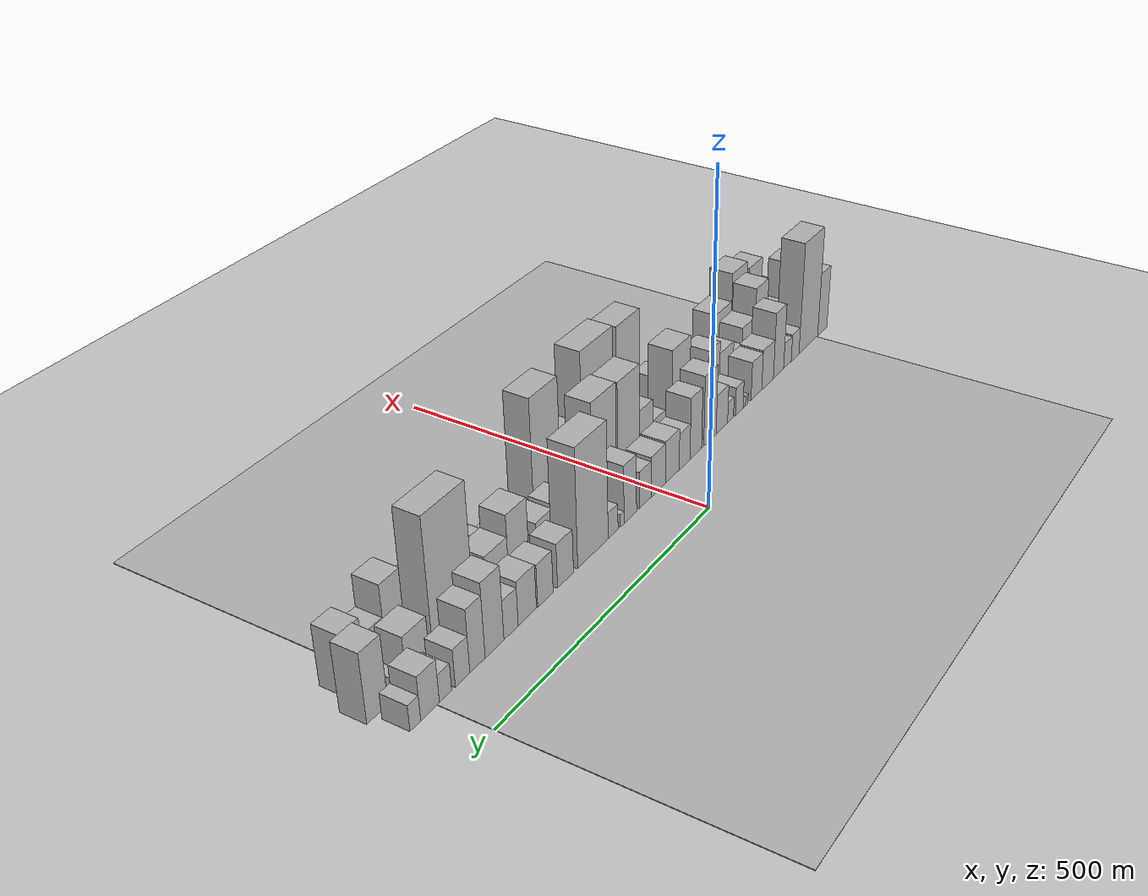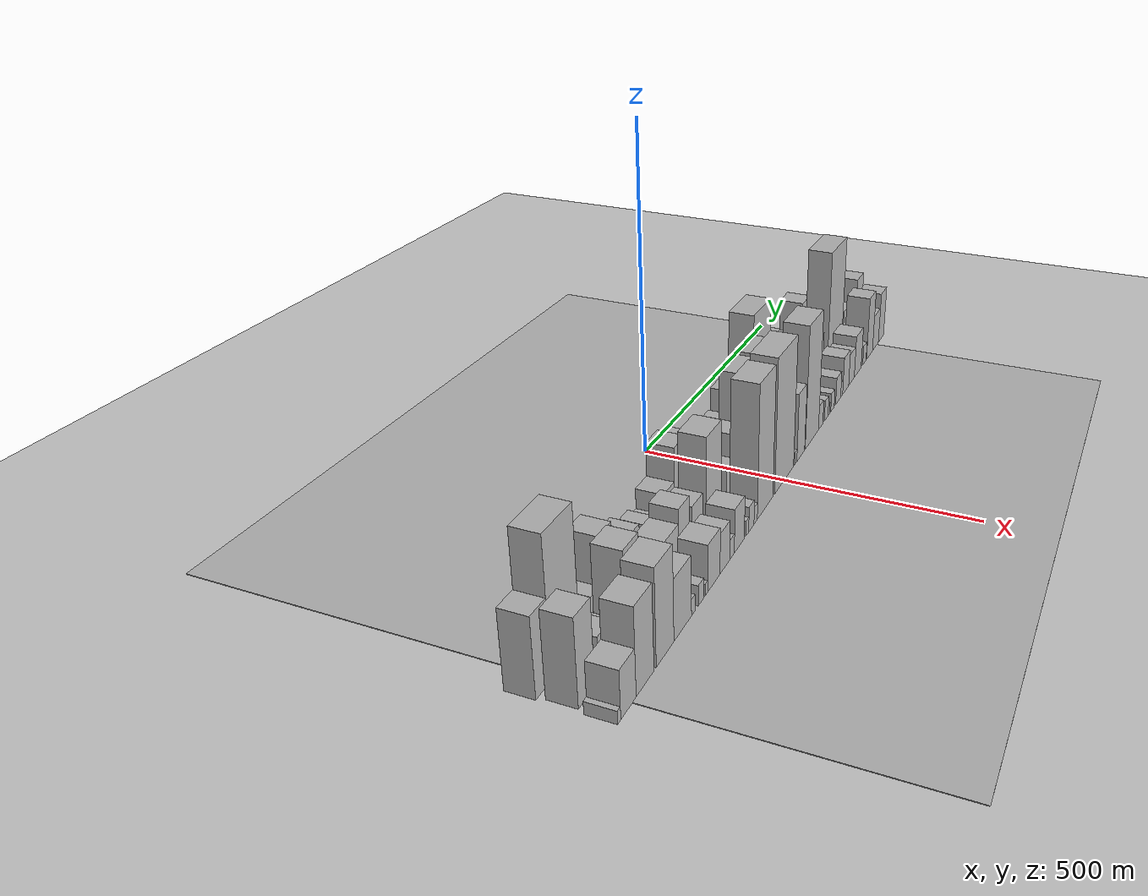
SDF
<?xml version="1.0" encoding="utf-8"?>

<sdf version="1.6">

   <world name="default">

      <gui fullscreen="0">

         <camera name="user_camera">

            <pose>-15 0 4.57585 0 0 0</pose>

            <view_controller>orbit</view_controller>

         </camera>

      </gui>

      <scene>

         <sky>

           <clouds>

             <speed>12</speed>

           </clouds>

         </sky>

         <ambient>0.4 0.4 0.4 1</ambient>

         <background>0.7 0.7 0.7 1</background>

         <shadows>1</shadows>

      </scene>

      <gravity>0 0 -9.8066</gravity>

      <magnetic_field>6e-06 2.3e-05 -4.2e-05</magnetic_field>

      <physics default="0" name="default_physics" type="ode">

         <ode>

            <solver>

               <type>quick</type>

               <iters>10</iters>

               <sor>1.0</sor>

               <use_dynamic_moi_rescaling>0</use_dynamic_moi_rescaling>

            </solver>

            <constraints>

               <cfm>0</cfm>

               <erp>0.2</erp>

               <contact_max_correcting_vel>100</contact_max_correcting_vel>

               <contact_surface_layer>0.001</contact_surface_layer>

            </constraints>

         </ode>

         <max_step_size>0.004</max_step_size>

         <real_time_factor>1</real_time_factor>

         <real_time_update_rate>250</real_time_update_rate>

      </physics>

      <light name="sun" type="directional">

         <cast_shadows>1</cast_shadows>

         <pose>0 0 10 0 0 0</pose>

         <diffuse>0.8 0.8 0.8 1</diffuse>

         <specular>0.2 0.2 0.2 1</specular>

         <attenuation>

            <range>1000</range>

            <constant>0.9</constant>

            <linear>0.01</linear>

            <quadratic>0.001</quadratic>

         </attenuation>

         <direction>-0.5 0.1 -0.9</direction>

      </light>

      <include>

         <name>ground_plane_1</name>

         <uri>model://HANNAS_ground_plane</uri>

         <pose>0 0 0  0 0 0</pose>

      </include>

      <include>

         <name>ground_plane_2</name>

         <uri>model://HANNAS_ground_plane</uri>

         <pose>100 0 0  0 0 0</pose>

      </include>

      <model name="building_1">

         <static>1</static>

         <pose frame="">100.0000 -518.8748 0 0.000000 0.000000 0.000000</pose>

         <link name="link">

            <pose frame="">0 0 55.50 0 0 0</pose>

            <collision name="collision">

               <geometry>

                  <box>

                     <size>40.0000 34.2505 111.0000</size>

                  </box>

               </geometry>

               <max_contacts>10</max_contacts>

               <surface>

                  <contact>

                     <ode/>

                  </contact>

                  <bounce/>

                  <friction>

                     <torsional>

                        <ode/>

                     </torsional>

                     <ode/>

                  </friction>

               </surface>

            </collision>

            <visual name="visual">

               <cast_shadows>0</cast_shadows>

               <geometry>

                  <box>

                     <size>40.0000 34.2505 111.0000</size>

                  </box>

               </geometry>

               <material>

                  <script>

                     <uri>model://HANNAS_wall/materials/scripts</uri>

                     <uri>model://HANNAS_wall/materials/textures</uri>

                     <name>vrc/HANNAS_wall</name>

                  </script>

               </material>

            </visual>

            <self_collide>0</self_collide>

            <enable_wind>0</enable_wind>

            <kinematic>0</kinematic>

         </link>

      </model>

      <model name="building_2">

         <static>1</static>

         <pose frame="">100.0000 -468.1727 0 0.000000 0.000000 0.000000</pose>

         <link name="link">

            <pose frame="">0 0 96.00 0 0 0</pose>

            <collision name="collision">

               <geometry>

                  <box>

                     <size>40.0000 67.1537 192.0000</size>

                  </box>

               </geometry>

               <max_contacts>10</max_contacts>

               <surface>

                  <contact>

                     <ode/>

                  </contact>

                  <bounce/>

                  <friction>

                     <torsional>

                        <ode/>

                     </torsional>

                     <ode/>

                  </friction>

               </surface>

            </collision>

            <visual name="visual">

               <cast_shadows>0</cast_shadows>

               <geometry>

                  <box>

                     <size>40.0000 67.1537 192.0000</size>

                  </box>

               </geometry>

               <material>

                  <script>

                     <uri>model://HANNAS_wall/materials/scripts</uri>

                     <uri>model://HANNAS_wall/materials/textures</uri>

                     <name>vrc/HANNAS_wall</name>

                  </script>

               </material>

            </visual>

            <self_collide>0</self_collide>

            <enable_wind>0</enable_wind>

            <kinematic>0</kinematic>

         </link>

      </model>

      <model name="building_3">

         <static>1</static>

         <pose frame="">100.0000 -420.9306 0 0.000000 0.000000 0.000000</pose>

         <link name="link">

            <pose frame="">0 0 24.00 0 0 0</pose>

            <collision name="collision">

               <geometry>

                  <box>

                     <size>40.0000 27.3303 48.0000</size>

                  </box>

               </geometry>

               <max_contacts>10</max_contacts>

               <surface>

                  <contact>

                     <ode/>

                  </contact>

                  <bounce/>

                  <friction>

                     <torsional>

                        <ode/>

                     </torsional>

                     <ode/>

                  </friction>

               </surface>

            </collision>

            <visual name="visual">

               <cast_shadows>0</cast_shadows>

               <geometry>

                  <box>

                     <size>40.0000 27.3303 48.0000</size>

                  </box>

               </geometry>

               <material>

                  <script>

                     <uri>model://HANNAS_wall/materials/scripts</uri>

                     <uri>model://HANNAS_wall/materials/textures</uri>

                     <name>vrc/HANNAS_wall</name>

                  </script>

               </material>

            </visual>

            <self_collide>0</self_collide>

            <enable_wind>0</enable_wind>

            <kinematic>0</kinematic>

         </link>

      </model>

      <model name="building_4">

         <static>1</static>

         <pose frame="">100.0000 -394.1880 0 0.000000 0.000000 0.000000</pose>

         <link name="link">

            <pose frame="">0 0 22.50 0 0 0</pose>

            <collision name="collision">

               <geometry>

                  <box>

                     <size>40.0000 26.1550 45.0000</size>

                  </box>

               </geometry>

               <max_contacts>10</max_contacts>

               <surface>

                  <contact>

                     <ode/>

                  </contact>

                  <bounce/>

                  <friction>

                     <torsional>

                        <ode/>

                     </torsional>

                     <ode/>

                  </friction>

               </surface>

            </collision>

            <visual name="visual">

               <cast_shadows>0</cast_shadows>

               <geometry>

                  <box>

                     <size>40.0000 26.1550 45.0000</size>

                  </box>

               </geometry>

               <material>

                  <script>

                     <uri>model://HANNAS_wall/materials/scripts</uri>

                     <uri>model://HANNAS_wall/materials/textures</uri>

                     <name>vrc/HANNAS_wall</name>

                  </script>

               </material>

            </visual>

            <self_collide>0</self_collide>

            <enable_wind>0</enable_wind>

            <kinematic>0</kinematic>

         </link>

      </model>

      <model name="building_5">

         <static>1</static>

         <pose frame="">100.0000 -363.7829 0 0.000000 0.000000 0.000000</pose>

         <link name="link">

            <pose frame="">0 0 57.00 0 0 0</pose>

            <collision name="collision">

               <geometry>

                  <box>

                     <size>40.0000 34.6551 114.0000</size>

                  </box>

               </geometry>

               <max_contacts>10</max_contacts>

               <surface>

                  <contact>

                     <ode/>

                  </contact>

                  <bounce/>

                  <friction>

                     <torsional>

                        <ode/>

                     </torsional>

                     <ode/>

                  </friction>

               </surface>

            </collision>

            <visual name="visual">

               <cast_shadows>0</cast_shadows>

               <geometry>

                  <box>

                     <size>40.0000 34.6551 114.0000</size>

                  </box>

               </geometry>

               <material>

                  <script>

                     <uri>model://HANNAS_wall/materials/scripts</uri>

                     <uri>model://HANNAS_wall/materials/textures</uri>

                     <name>vrc/HANNAS_wall</name>

                  </script>

               </material>

            </visual>

            <self_collide>0</self_collide>

            <enable_wind>0</enable_wind>

            <kinematic>0</kinematic>

         </link>

      </model>

      <model name="building_6">

         <static>1</static>

         <pose frame="">100.0000 -327.1159 0 0.000000 0.000000 0.000000</pose>

         <link name="link">

            <pose frame="">0 0 34.50 0 0 0</pose>

            <collision name="collision">

               <geometry>

                  <box>

                     <size>40.0000 38.6789 69.0000</size>

                  </box>

               </geometry>

               <max_contacts>10</max_contacts>

               <surface>

                  <contact>

                     <ode/>

                  </contact>

                  <bounce/>

                  <friction>

                     <torsional>

                        <ode/>

                     </torsional>

                     <ode/>

                  </friction>

               </surface>

            </collision>

            <visual name="visual">

               <cast_shadows>0</cast_shadows>

               <geometry>

                  <box>

                     <size>40.0000 38.6789 69.0000</size>

                  </box>

               </geometry>

               <material>

                  <script>

                     <uri>model://HANNAS_wall/materials/scripts</uri>

                     <uri>model://HANNAS_wall/materials/textures</uri>

                     <name>vrc/HANNAS_wall</name>

                  </script>

               </material>

            </visual>

            <self_collide>0</self_collide>

            <enable_wind>0</enable_wind>

            <kinematic>0</kinematic>

         </link>

      </model>

      <model name="building_7">

         <static>1</static>

         <pose frame="">100.0000 -290.4375 0 0.000000 0.000000 0.000000</pose>

         <link name="link">

            <pose frame="">0 0 33.00 0 0 0</pose>

            <collision name="collision">

               <geometry>

                  <box>

                     <size>40.0000 34.6778 66.0000</size>

                  </box>

               </geometry>

               <max_contacts>10</max_contacts>

               <surface>

                  <contact>

                     <ode/>

                  </contact>

                  <bounce/>

                  <friction>

                     <torsional>

                        <ode/>

                     </torsional>

                     <ode/>

                  </friction>

               </surface>

            </collision>

            <visual name="visual">

               <cast_shadows>0</cast_shadows>

               <geometry>

                  <box>

                     <size>40.0000 34.6778 66.0000</size>

                  </box>

               </geometry>

               <material>

                  <script>

                     <uri>model://HANNAS_wall/materials/scripts</uri>

                     <uri>model://HANNAS_wall/materials/textures</uri>

                     <name>vrc/HANNAS_wall</name>

                  </script>

               </material>

            </visual>

            <self_collide>0</self_collide>

            <enable_wind>0</enable_wind>

            <kinematic>0</kinematic>

         </link>

      </model>

      <model name="building_8">

         <static>1</static>

         <pose frame="">100.0000 -259.2827 0 0.000000 0.000000 0.000000</pose>

         <link name="link">

            <pose frame="">0 0 9.00 0 0 0</pose>

            <collision name="collision">

               <geometry>

                  <box>

                     <size>40.0000 7.6319 18.0000</size>

                  </box>

               </geometry>

               <max_contacts>10</max_contacts>

               <surface>

                  <contact>

                     <ode/>

                  </contact>

                  <bounce/>

                  <friction>

                     <torsional>

                        <ode/>

                     </torsional>

                     <ode/>

                  </friction>

               </surface>

            </collision>

            <visual name="visual">

               <cast_shadows>0</cast_shadows>

               <geometry>

                  <box>

                     <size>40.0000 7.6319 18.0000</size>

                  </box>

               </geometry>

               <material>

                  <script>

                     <uri>model://HANNAS_wall/materials/scripts</uri>

                     <uri>model://HANNAS_wall/materials/textures</uri>

                     <name>vrc/HANNAS_wall</name>

                  </script>

               </material>

            </visual>

            <self_collide>0</self_collide>

            <enable_wind>0</enable_wind>

            <kinematic>0</kinematic>

         </link>

      </model>

      <model name="building_9">

         <static>1</static>

         <pose frame="">100.0000 -251.6473 0 0.000000 0.000000 0.000000</pose>

         <link name="link">

            <pose frame="">0 0 9.00 0 0 0</pose>

            <collision name="collision">

               <geometry>

                  <box>

                     <size>40.0000 7.6390 18.0000</size>

                  </box>

               </geometry>

               <max_contacts>10</max_contacts>

               <surface>

                  <contact>

                     <ode/>

                  </contact>

                  <bounce/>

                  <friction>

                     <torsional>

                        <ode/>

                     </torsional>

                     <ode/>

                  </friction>

               </surface>

            </collision>

            <visual name="visual">

               <cast_shadows>0</cast_shadows>

               <geometry>

                  <box>

                     <size>40.0000 7.6390 18.0000</size>

                  </box>

               </geometry>

               <material>

                  <script>

                     <uri>model://HANNAS_wall/materials/scripts</uri>

                     <uri>model://HANNAS_wall/materials/textures</uri>

                     <name>vrc/HANNAS_wall</name>

                  </script>

               </material>

            </visual>

            <self_collide>0</self_collide>

            <enable_wind>0</enable_wind>

            <kinematic>0</kinematic>

         </link>

      </model>

      <model name="building_10">

         <static>1</static>

         <pose frame="">100.0000 -235.7651 0 0.000000 0.000000 0.000000</pose>

         <link name="link">

            <pose frame="">0 0 24.00 0 0 0</pose>

            <collision name="collision">

               <geometry>

                  <box>

                     <size>40.0000 24.1254 48.0000</size>

                  </box>

               </geometry>

               <max_contacts>10</max_contacts>

               <surface>

                  <contact>

                     <ode/>

                  </contact>

                  <bounce/>

                  <friction>

                     <torsional>

                        <ode/>

                     </torsional>

                     <ode/>

                  </friction>

               </surface>

            </collision>

            <visual name="visual">

               <cast_shadows>0</cast_shadows>

               <geometry>

                  <box>

                     <size>40.0000 24.1254 48.0000</size>

                  </box>

               </geometry>

               <material>

                  <script>

                     <uri>model://HANNAS_wall/materials/scripts</uri>

                     <uri>model://HANNAS_wall/materials/textures</uri>

                     <name>vrc/HANNAS_wall</name>

                  </script>

               </material>

            </visual>

            <self_collide>0</self_collide>

            <enable_wind>0</enable_wind>

            <kinematic>0</kinematic>

         </link>

      </model>

      <model name="building_11">

         <static>1</static>

         <pose frame="">100.0000 -208.6432 0 0.000000 0.000000 0.000000</pose>

         <link name="link">

            <pose frame="">0 0 18.00 0 0 0</pose>

            <collision name="collision">

               <geometry>

                  <box>

                     <size>40.0000 18.1185 36.0000</size>

                  </box>

               </geometry>

               <max_contacts>10</max_contacts>

               <surface>

                  <contact>

                     <ode/>

                  </contact>

                  <bounce/>

                  <friction>

                     <torsional>

                        <ode/>

                     </torsional>

                     <ode/>

                  </friction>

               </surface>

            </collision>

            <visual name="visual">

               <cast_shadows>0</cast_shadows>

               <geometry>

                  <box>

                     <size>40.0000 18.1185 36.0000</size>

                  </box>

               </geometry>

               <material>

                  <script>

                     <uri>model://HANNAS_wall/materials/scripts</uri>

                     <uri>model://HANNAS_wall/materials/textures</uri>

                     <name>vrc/HANNAS_wall</name>

                  </script>

               </material>

            </visual>

            <self_collide>0</self_collide>

            <enable_wind>0</enable_wind>

            <kinematic>0</kinematic>

         </link>

      </model>

      <model name="building_12">

         <static>1</static>

         <pose frame="">100.0000 -182.1836 0 0.000000 0.000000 0.000000</pose>

         <link name="link">

            <pose frame="">0 0 33.00 0 0 0</pose>

            <collision name="collision">

               <geometry>

                  <box>

                     <size>40.0000 34.8006 66.0000</size>

                  </box>

               </geometry>

               <max_contacts>10</max_contacts>

               <surface>

                  <contact>

                     <ode/>

                  </contact>

                  <bounce/>

                  <friction>

                     <torsional>

                        <ode/>

                     </torsional>

                     <ode/>

                  </friction>

               </surface>

            </collision>

            <visual name="visual">

               <cast_shadows>0</cast_shadows>

               <geometry>

                  <box>

                     <size>40.0000 34.8006 66.0000</size>

                  </box>

               </geometry>

               <material>

                  <script>

                     <uri>model://HANNAS_wall/materials/scripts</uri>

                     <uri>model://HANNAS_wall/materials/textures</uri>

                     <name>vrc/HANNAS_wall</name>

                  </script>

               </material>

            </visual>

            <self_collide>0</self_collide>

            <enable_wind>0</enable_wind>

            <kinematic>0</kinematic>

         </link>

      </model>

      <model name="building_13">

         <static>1</static>

         <pose frame="">100.0000 -146.3476 0 0.000000 0.000000 0.000000</pose>

         <link name="link">

            <pose frame="">0 0 58.50 0 0 0</pose>

            <collision name="collision">

               <geometry>

                  <box>

                     <size>40.0000 36.8714 117.0000</size>

                  </box>

               </geometry>

               <max_contacts>10</max_contacts>

               <surface>

                  <contact>

                     <ode/>

                  </contact>

                  <bounce/>

                  <friction>

                     <torsional>

                        <ode/>

                     </torsional>

                     <ode/>

                  </friction>

               </surface>

            </collision>

            <visual name="visual">

               <cast_shadows>0</cast_shadows>

               <geometry>

                  <box>

                     <size>40.0000 36.8714 117.0000</size>

                  </box>

               </geometry>

               <material>

                  <script>

                     <uri>model://HANNAS_wall/materials/scripts</uri>

                     <uri>model://HANNAS_wall/materials/textures</uri>

                     <name>vrc/HANNAS_wall</name>

                  </script>

               </material>

            </visual>

            <self_collide>0</self_collide>

            <enable_wind>0</enable_wind>

            <kinematic>0</kinematic>

         </link>

      </model>

      <model name="building_14">

         <static>1</static>

         <pose frame="">100.0000 -124.7498 0 0.000000 0.000000 0.000000</pose>

         <link name="link">

            <pose frame="">0 0 7.50 0 0 0</pose>

            <collision name="collision">

               <geometry>

                  <box>

                     <size>40.0000 6.3241 15.0000</size>

                  </box>

               </geometry>

               <max_contacts>10</max_contacts>

               <surface>

                  <contact>

                     <ode/>

                  </contact>

                  <bounce/>

                  <friction>

                     <torsional>

                        <ode/>

                     </torsional>

                     <ode/>

                  </friction>

               </surface>

            </collision>

            <visual name="visual">

               <cast_shadows>0</cast_shadows>

               <geometry>

                  <box>

                     <size>40.0000 6.3241 15.0000</size>

                  </box>

               </geometry>

               <material>

                  <script>

                     <uri>model://HANNAS_wall/materials/scripts</uri>

                     <uri>model://HANNAS_wall/materials/textures</uri>

                     <name>vrc/HANNAS_wall</name>

                  </script>

               </material>

            </visual>

            <self_collide>0</self_collide>

            <enable_wind>0</enable_wind>

            <kinematic>0</kinematic>

         </link>

      </model>

      <model name="building_15">

         <static>1</static>

         <pose frame="">100.0000 -104.9406 0 0.000000 0.000000 0.000000</pose>

         <link name="link">

            <pose frame="">0 0 51.00 0 0 0</pose>

            <collision name="collision">

               <geometry>

                  <box>

                     <size>40.0000 33.2942 102.0000</size>

                  </box>

               </geometry>

               <max_contacts>10</max_contacts>

               <surface>

                  <contact>

                     <ode/>

                  </contact>

                  <bounce/>

                  <friction>

                     <torsional>

                        <ode/>

                     </torsional>

                     <ode/>

                  </friction>

               </surface>

            </collision>

            <visual name="visual">

               <cast_shadows>0</cast_shadows>

               <geometry>

                  <box>

                     <size>40.0000 33.2942 102.0000</size>

                  </box>

               </geometry>

               <material>

                  <script>

                     <uri>model://HANNAS_wall/materials/scripts</uri>

                     <uri>model://HANNAS_wall/materials/textures</uri>

                     <name>vrc/HANNAS_wall</name>

                  </script>

               </material>

            </visual>

            <self_collide>0</self_collide>

            <enable_wind>0</enable_wind>

            <kinematic>0</kinematic>

         </link>

      </model>

      <model name="building_16">

         <static>1</static>

         <pose frame="">100.0000 -72.9207 0 0.000000 0.000000 0.000000</pose>

         <link name="link">

            <pose frame="">0 0 30.00 0 0 0</pose>

            <collision name="collision">

               <geometry>

                  <box>

                     <size>40.0000 30.7456 60.0000</size>

                  </box>

               </geometry>

               <max_contacts>10</max_contacts>

               <surface>

                  <contact>

                     <ode/>

                  </contact>

                  <bounce/>

                  <friction>

                     <torsional>

                        <ode/>

                     </torsional>

                     <ode/>

                  </friction>

               </surface>

            </collision>

            <visual name="visual">

               <cast_shadows>0</cast_shadows>

               <geometry>

                  <box>

                     <size>40.0000 30.7456 60.0000</size>

                  </box>

               </geometry>

               <material>

                  <script>

                     <uri>model://HANNAS_wall/materials/scripts</uri>

                     <uri>model://HANNAS_wall/materials/textures</uri>

                     <name>vrc/HANNAS_wall</name>

                  </script>

               </material>

            </visual>

            <self_collide>0</self_collide>

            <enable_wind>0</enable_wind>

            <kinematic>0</kinematic>

         </link>

      </model>

      <model name="building_17">

         <static>1</static>

         <pose frame="">100.0000 -38.5526 0 0.000000 0.000000 0.000000</pose>

         <link name="link">

            <pose frame="">0 0 34.50 0 0 0</pose>

            <collision name="collision">

               <geometry>

                  <box>

                     <size>40.0000 37.9906 69.0000</size>

                  </box>

               </geometry>

               <max_contacts>10</max_contacts>

               <surface>

                  <contact>

                     <ode/>

                  </contact>

                  <bounce/>

                  <friction>

                     <torsional>

                        <ode/>

                     </torsional>

                     <ode/>

                  </friction>

               </surface>

            </collision>

            <visual name="visual">

               <cast_shadows>0</cast_shadows>

               <geometry>

                  <box>

                     <size>40.0000 37.9906 69.0000</size>

                  </box>

               </geometry>

               <material>

                  <script>

                     <uri>model://HANNAS_wall/materials/scripts</uri>

                     <uri>model://HANNAS_wall/materials/textures</uri>

                     <name>vrc/HANNAS_wall</name>

                  </script>

               </material>

            </visual>

            <self_collide>0</self_collide>

            <enable_wind>0</enable_wind>

            <kinematic>0</kinematic>

         </link>

      </model>

      <model name="building_18">

         <static>1</static>

         <pose frame="">100.0000 0.2296 0 0.000000 0.000000 0.000000</pose>

         <link name="link">

            <pose frame="">0 0 33.00 0 0 0</pose>

            <collision name="collision">

               <geometry>

                  <box>

                     <size>40.0000 39.5738 66.0000</size>

                  </box>

               </geometry>

               <max_contacts>10</max_contacts>

               <surface>

                  <contact>

                     <ode/>

                  </contact>

                  <bounce/>

                  <friction>

                     <torsional>

                        <ode/>

                     </torsional>

                     <ode/>

                  </friction>

               </surface>

            </collision>

            <visual name="visual">

               <cast_shadows>0</cast_shadows>

               <geometry>

                  <box>

                     <size>40.0000 39.5738 66.0000</size>

                  </box>

               </geometry>

               <material>

                  <script>

                     <uri>model://HANNAS_wall/materials/scripts</uri>

                     <uri>model://HANNAS_wall/materials/textures</uri>

                     <name>vrc/HANNAS_wall</name>

                  </script>

               </material>

            </visual>

            <self_collide>0</self_collide>

            <enable_wind>0</enable_wind>

            <kinematic>0</kinematic>

         </link>

      </model>

      <model name="building_19">

         <static>1</static>

         <pose frame="">100.0000 35.4518 0 0.000000 0.000000 0.000000</pose>

         <link name="link">

            <pose frame="">0 0 30.00 0 0 0</pose>

            <collision name="collision">

               <geometry>

                  <box>

                     <size>40.0000 30.8706 60.0000</size>

                  </box>

               </geometry>

               <max_contacts>10</max_contacts>

               <surface>

                  <contact>

                     <ode/>

                  </contact>

                  <bounce/>

                  <friction>

                     <torsional>

                        <ode/>

                     </torsional>

                     <ode/>

                  </friction>

               </surface>

            </collision>

            <visual name="visual">

               <cast_shadows>0</cast_shadows>

               <geometry>

                  <box>

                     <size>40.0000 30.8706 60.0000</size>

                  </box>

               </geometry>

               <material>

                  <script>

                     <uri>model://HANNAS_wall/materials/scripts</uri>

                     <uri>model://HANNAS_wall/materials/textures</uri>

                     <name>vrc/HANNAS_wall</name>

                  </script>

               </material>

            </visual>

            <self_collide>0</self_collide>

            <enable_wind>0</enable_wind>

            <kinematic>0</kinematic>

         </link>

      </model>

      <model name="building_20">

         <static>1</static>

         <pose frame="">100.0000 73.9305 0 0.000000 0.000000 0.000000</pose>

         <link name="link">

            <pose frame="">0 0 46.50 0 0 0</pose>

            <collision name="collision">

               <geometry>

                  <box>

                     <size>40.0000 32.0868 93.0000</size>

                  </box>

               </geometry>

               <max_contacts>10</max_contacts>

               <surface>

                  <contact>

                     <ode/>

                  </contact>

                  <bounce/>

                  <friction>

                     <torsional>

                        <ode/>

                     </torsional>

                     <ode/>

                  </friction>

               </surface>

            </collision>

            <visual name="visual">

               <cast_shadows>0</cast_shadows>

               <geometry>

                  <box>

                     <size>40.0000 32.0868 93.0000</size>

                  </box>

               </geometry>

               <material>

                  <script>

                     <uri>model://HANNAS_wall/materials/scripts</uri>

                     <uri>model://HANNAS_wall/materials/textures</uri>

                     <name>vrc/HANNAS_wall</name>

                  </script>

               </material>

            </visual>

            <self_collide>0</self_collide>

            <enable_wind>0</enable_wind>

            <kinematic>0</kinematic>

         </link>

      </model>

      <model name="building_21">

         <static>1</static>

         <pose frame="">100.0000 94.6951 0 0.000000 0.000000 0.000000</pose>

         <link name="link">

            <pose frame="">0 0 10.50 0 0 0</pose>

            <collision name="collision">

               <geometry>

                  <box>

                     <size>40.0000 9.4425 21.0000</size>

                  </box>

               </geometry>

               <max_contacts>10</max_contacts>

               <surface>

                  <contact>

                     <ode/>

                  </contact>

                  <bounce/>

                  <friction>

                     <torsional>

                        <ode/>

                     </torsional>

                     <ode/>

                  </friction>

               </surface>

            </collision>

            <visual name="visual">

               <cast_shadows>0</cast_shadows>

               <geometry>

                  <box>

                     <size>40.0000 9.4425 21.0000</size>

                  </box>

               </geometry>

               <material>

                  <script>

                     <uri>model://HANNAS_wall/materials/scripts</uri>

                     <uri>model://HANNAS_wall/materials/textures</uri>

                     <name>vrc/HANNAS_wall</name>

                  </script>

               </material>

            </visual>

            <self_collide>0</self_collide>

            <enable_wind>0</enable_wind>

            <kinematic>0</kinematic>

         </link>

      </model>

      <model name="building_22">

         <static>1</static>

         <pose frame="">100.0000 117.7082 0 0.000000 0.000000 0.000000</pose>

         <link name="link">

            <pose frame="">0 0 21.00 0 0 0</pose>

            <collision name="collision">

               <geometry>

                  <box>

                     <size>40.0000 24.5837 42.0000</size>

                  </box>

               </geometry>

               <max_contacts>10</max_contacts>

               <surface>

                  <contact>

                     <ode/>

                  </contact>

                  <bounce/>

                  <friction>

                     <torsional>

                        <ode/>

                     </torsional>

                     <ode/>

                  </friction>

               </surface>

            </collision>

            <visual name="visual">

               <cast_shadows>0</cast_shadows>

               <geometry>

                  <box>

                     <size>40.0000 24.5837 42.0000</size>

                  </box>

               </geometry>

               <material>

                  <script>

                     <uri>model://HANNAS_wall/materials/scripts</uri>

                     <uri>model://HANNAS_wall/materials/textures</uri>

                     <name>vrc/HANNAS_wall</name>

                  </script>

               </material>

            </visual>

            <self_collide>0</self_collide>

            <enable_wind>0</enable_wind>

            <kinematic>0</kinematic>

         </link>

      </model>

      <model name="building_23">

         <static>1</static>

         <pose frame="">100.0000 166.8119 0 0.000000 0.000000 0.000000</pose>

         <link name="link">

            <pose frame="">0 0 93.00 0 0 0</pose>

            <collision name="collision">

               <geometry>

                  <box>

                     <size>40.0000 73.6238 186.0000</size>

                  </box>

               </geometry>

               <max_contacts>10</max_contacts>

               <surface>

                  <contact>

                     <ode/>

                  </contact>

                  <bounce/>

                  <friction>

                     <torsional>

                        <ode/>

                     </torsional>

                     <ode/>

                  </friction>

               </surface>

            </collision>

            <visual name="visual">

               <cast_shadows>0</cast_shadows>

               <geometry>

                  <box>

                     <size>40.0000 73.6238 186.0000</size>

                  </box>

               </geometry>

               <material>

                  <script>

                     <uri>model://HANNAS_wall/materials/scripts</uri>

                     <uri>model://HANNAS_wall/materials/textures</uri>

                     <name>vrc/HANNAS_wall</name>

                  </script>

               </material>

            </visual>

            <self_collide>0</self_collide>

            <enable_wind>0</enable_wind>

            <kinematic>0</kinematic>

         </link>

      </model>

      <model name="building_24">

         <static>1</static>

         <pose frame="">100.0000 231.9970 0 0.000000 0.000000 0.000000</pose>

         <link name="link">

            <pose frame="">0 0 34.50 0 0 0</pose>

            <collision name="collision">

               <geometry>

                  <box>

                     <size>40.0000 36.7465 69.0000</size>

                  </box>

               </geometry>

               <max_contacts>10</max_contacts>

               <surface>

                  <contact>

                     <ode/>

                  </contact>

                  <bounce/>

                  <friction>

                     <torsional>

                        <ode/>

                     </torsional>

                     <ode/>

                  </friction>

               </surface>

            </collision>

            <visual name="visual">

               <cast_shadows>0</cast_shadows>

               <geometry>

                  <box>

                     <size>40.0000 36.7465 69.0000</size>

                  </box>

               </geometry>

               <material>

                  <script>

                     <uri>model://HANNAS_wall/materials/scripts</uri>

                     <uri>model://HANNAS_wall/materials/textures</uri>

                     <name>vrc/HANNAS_wall</name>

                  </script>

               </material>

            </visual>

            <self_collide>0</self_collide>

            <enable_wind>0</enable_wind>

            <kinematic>0</kinematic>

         </link>

      </model>

      <model name="building_25">

         <static>1</static>

         <pose frame="">100.0000 277.5729 0 0.000000 0.000000 0.000000</pose>

         <link name="link">

            <pose frame="">0 0 33.00 0 0 0</pose>

            <collision name="collision">

               <geometry>

                  <box>

                     <size>40.0000 34.4054 66.0000</size>

                  </box>

               </geometry>

               <max_contacts>10</max_contacts>

               <surface>

                  <contact>

                     <ode/>

                  </contact>

                  <bounce/>

                  <friction>

                     <torsional>

                        <ode/>

                     </torsional>

                     <ode/>

                  </friction>

               </surface>

            </collision>

            <visual name="visual">

               <cast_shadows>0</cast_shadows>

               <geometry>

                  <box>

                     <size>40.0000 34.4054 66.0000</size>

                  </box>

               </geometry>

               <material>

                  <script>

                     <uri>model://HANNAS_wall/materials/scripts</uri>

                     <uri>model://HANNAS_wall/materials/textures</uri>

                     <name>vrc/HANNAS_wall</name>

                  </script>

               </material>

            </visual>

            <self_collide>0</self_collide>

            <enable_wind>0</enable_wind>

            <kinematic>0</kinematic>

         </link>

      </model>

      <model name="building_26">

         <static>1</static>

         <pose frame="">100.0000 317.5310 0 0.000000 0.000000 0.000000</pose>

         <link name="link">

            <pose frame="">0 0 34.50 0 0 0</pose>

            <collision name="collision">

               <geometry>

                  <box>

                     <size>40.0000 39.5108 69.0000</size>

                  </box>

               </geometry>

               <max_contacts>10</max_contacts>

               <surface>

                  <contact>

                     <ode/>

                  </contact>

                  <bounce/>

                  <friction>

                     <torsional>

                        <ode/>

                     </torsional>

                     <ode/>

                  </friction>

               </surface>

            </collision>

            <visual name="visual">

               <cast_shadows>0</cast_shadows>

               <geometry>

                  <box>

                     <size>40.0000 39.5108 69.0000</size>

                  </box>

               </geometry>

               <material>

                  <script>

                     <uri>model://HANNAS_wall/materials/scripts</uri>

                     <uri>model://HANNAS_wall/materials/textures</uri>

                     <name>vrc/HANNAS_wall</name>

                  </script>

               </material>

            </visual>

            <self_collide>0</self_collide>

            <enable_wind>0</enable_wind>

            <kinematic>0</kinematic>

         </link>

      </model>

      <model name="building_27">

         <static>1</static>

         <pose frame="">100.0000 352.3876 0 0.000000 0.000000 0.000000</pose>

         <link name="link">

            <pose frame="">0 0 30.00 0 0 0</pose>

            <collision name="collision">

               <geometry>

                  <box>

                     <size>40.0000 30.2024 60.0000</size>

                  </box>

               </geometry>

               <max_contacts>10</max_contacts>

               <surface>

                  <contact>

                     <ode/>

                  </contact>

                  <bounce/>

                  <friction>

                     <torsional>

                        <ode/>

                     </torsional>

                     <ode/>

                  </friction>

               </surface>

            </collision>

            <visual name="visual">

               <cast_shadows>0</cast_shadows>

               <geometry>

                  <box>

                     <size>40.0000 30.2024 60.0000</size>

                  </box>

               </geometry>

               <material>

                  <script>

                     <uri>model://HANNAS_wall/materials/scripts</uri>

                     <uri>model://HANNAS_wall/materials/textures</uri>

                     <name>vrc/HANNAS_wall</name>

                  </script>

               </material>

            </visual>

            <self_collide>0</self_collide>

            <enable_wind>0</enable_wind>

            <kinematic>0</kinematic>

         </link>

      </model>

      <model name="building_28">

         <static>1</static>

         <pose frame="">100.0000 386.8651 0 0.000000 0.000000 0.000000</pose>

         <link name="link">

            <pose frame="">0 0 57.00 0 0 0</pose>

            <collision name="collision">

               <geometry>

                  <box>

                     <size>40.0000 38.7527 114.0000</size>

                  </box>

               </geometry>

               <max_contacts>10</max_contacts>

               <surface>

                  <contact>

                     <ode/>

                  </contact>

                  <bounce/>

                  <friction>

                     <torsional>

                        <ode/>

                     </torsional>

                     <ode/>

                  </friction>

               </surface>

            </collision>

            <visual name="visual">

               <cast_shadows>0</cast_shadows>

               <geometry>

                  <box>

                     <size>40.0000 38.7527 114.0000</size>

                  </box>

               </geometry>

               <material>

                  <script>

                     <uri>model://HANNAS_wall/materials/scripts</uri>

                     <uri>model://HANNAS_wall/materials/textures</uri>

                     <name>vrc/HANNAS_wall</name>

                  </script>

               </material>

            </visual>

            <self_collide>0</self_collide>

            <enable_wind>0</enable_wind>

            <kinematic>0</kinematic>

         </link>

      </model>

      <model name="building_29">

         <static>1</static>

         <pose frame="">100.0000 421.6258 0 0.000000 0.000000 0.000000</pose>

         <link name="link">

            <pose frame="">0 0 48.00 0 0 0</pose>

            <collision name="collision">

               <geometry>

                  <box>

                     <size>40.0000 30.7687 96.0000</size>

                  </box>

               </geometry>

               <max_contacts>10</max_contacts>

               <surface>

                  <contact>

                     <ode/>

                  </contact>

                  <bounce/>

                  <friction>

                     <torsional>

                        <ode/>

                     </torsional>

                     <ode/>

                  </friction>

               </surface>

            </collision>

            <visual name="visual">

               <cast_shadows>0</cast_shadows>

               <geometry>

                  <box>

                     <size>40.0000 30.7687 96.0000</size>

                  </box>

               </geometry>

               <material>

                  <script>

                     <uri>model://HANNAS_wall/materials/scripts</uri>

                     <uri>model://HANNAS_wall/materials/textures</uri>

                     <name>vrc/HANNAS_wall</name>

                  </script>

               </material>

            </visual>

            <self_collide>0</self_collide>

            <enable_wind>0</enable_wind>

            <kinematic>0</kinematic>

         </link>

      </model>

      <model name="building_30">

         <static>1</static>

         <pose frame="">100.0000 451.2960 0 0.000000 0.000000 0.000000</pose>

         <link name="link">

            <pose frame="">0 0 28.50 0 0 0</pose>

            <collision name="collision">

               <geometry>

                  <box>

                     <size>40.0000 28.5716 57.0000</size>

                  </box>

               </geometry>

               <max_contacts>10</max_contacts>

               <surface>

                  <contact>

                     <ode/>

                  </contact>

                  <bounce/>

                  <friction>

                     <torsional>

                        <ode/>

                     </torsional>

                     <ode/>

                  </friction>

               </surface>

            </collision>

            <visual name="visual">

               <cast_shadows>0</cast_shadows>

               <geometry>

                  <box>

                     <size>40.0000 28.5716 57.0000</size>

                  </box>

               </geometry>

               <material>

                  <script>

                     <uri>model://HANNAS_wall/materials/scripts</uri>

                     <uri>model://HANNAS_wall/materials/textures</uri>

                     <name>vrc/HANNAS_wall</name>

                  </script>

               </material>

            </visual>

            <self_collide>0</self_collide>

            <enable_wind>0</enable_wind>

            <kinematic>0</kinematic>

         </link>

      </model>

      <model name="building_31">

         <static>1</static>

         <pose frame="">100.0000 484.3858 0 0.000000 0.000000 0.000000</pose>

         <link name="link">

            <pose frame="">0 0 21.00 0 0 0</pose>

            <collision name="collision">

               <geometry>

                  <box>

                     <size>40.0000 23.6079 42.0000</size>

                  </box>

               </geometry>

               <max_contacts>10</max_contacts>

               <surface>

                  <contact>

                     <ode/>

                  </contact>

                  <bounce/>

                  <friction>

                     <torsional>

                        <ode/>

                     </torsional>

                     <ode/>

                  </friction>

               </surface>

            </collision>

            <visual name="visual">

               <cast_shadows>0</cast_shadows>

               <geometry>

                  <box>

                     <size>40.0000 23.6079 42.0000</size>

                  </box>

               </geometry>

               <material>

                  <script>

                     <uri>model://HANNAS_wall/materials/scripts</uri>

                     <uri>model://HANNAS_wall/materials/textures</uri>

                     <name>vrc/HANNAS_wall</name>

                  </script>

               </material>

            </visual>

            <self_collide>0</self_collide>

            <enable_wind>0</enable_wind>

            <kinematic>0</kinematic>

         </link>

      </model>

      <model name="building_32">

         <static>1</static>

         <pose frame="">100.0000 513.6715 0 0.000000 0.000000 0.000000</pose>

         <link name="link">

            <pose frame="">0 0 33.00 0 0 0</pose>

            <collision name="collision">

               <geometry>

                  <box>

                     <size>40.0000 34.9635 66.0000</size>

                  </box>

               </geometry>

               <max_contacts>10</max_contacts>

               <surface>

                  <contact>

                     <ode/>

                  </contact>

                  <bounce/>

                  <friction>

                     <torsional>

                        <ode/>

                     </torsional>

                     <ode/>

                  </friction>

               </surface>

            </collision>

            <visual name="visual">

               <cast_shadows>0</cast_shadows>

               <geometry>

                  <box>

                     <size>40.0000 34.9635 66.0000</size>

                  </box>

               </geometry>

               <material>

                  <script>

                     <uri>model://HANNAS_wall/materials/scripts</uri>

                     <uri>model://HANNAS_wall/materials/textures</uri>

                     <name>vrc/HANNAS_wall</name>

                  </script>

               </material>

            </visual>

            <self_collide>0</self_collide>

            <enable_wind>0</enable_wind>

            <kinematic>0</kinematic>

         </link>

      </model>

      <model name="building_33">

         <static>1</static>

         <pose frame="">100.0000 541.0314 0 0.000000 0.000000 0.000000</pose>

         <link name="link">

            <pose frame="">0 0 19.50 0 0 0</pose>

            <collision name="collision">

               <geometry>

                  <box>

                     <size>40.0000 19.7562 39.0000</size>

                  </box>

               </geometry>

               <max_contacts>10</max_contacts>

               <surface>

                  <contact>

                     <ode/>

                  </contact>

                  <bounce/>

                  <friction>

                     <torsional>

                        <ode/>

                     </torsional>

                     <ode/>

                  </friction>

               </surface>

            </collision>

            <visual name="visual">

               <cast_shadows>0</cast_shadows>

               <geometry>

                  <box>

                     <size>40.0000 19.7562 39.0000</size>

                  </box>

               </geometry>

               <material>

                  <script>

                     <uri>model://HANNAS_wall/materials/scripts</uri>

                     <uri>model://HANNAS_wall/materials/textures</uri>

                     <name>vrc/HANNAS_wall</name>

                  </script>

               </material>

            </visual>

            <self_collide>0</self_collide>

            <enable_wind>0</enable_wind>

            <kinematic>0</kinematic>

         </link>

      </model>

      <model name="building_34">

         <static>1</static>

         <pose frame="">149.0000 -512.0264 0 0.000000 0.000000 0.000000</pose>

         <link name="link">

            <pose frame="">0 0 60.00 0 0 0</pose>

            <collision name="collision">

               <geometry>

                  <box>

                     <size>40.0000 37.9473 120.0000</size>

                  </box>

               </geometry>

               <max_contacts>10</max_contacts>

               <surface>

                  <contact>

                     <ode/>

                  </contact>

                  <bounce/>

                  <friction>

                     <torsional>

                        <ode/>

                     </torsional>

                     <ode/>

                  </friction>

               </surface>

            </collision>

            <visual name="visual">

               <cast_shadows>0</cast_shadows>

               <geometry>

                  <box>

                     <size>40.0000 37.9473 120.0000</size>

                  </box>

               </geometry>

               <material>

                  <script>

                     <uri>model://HANNAS_wall/materials/scripts</uri>

                     <uri>model://HANNAS_wall/materials/textures</uri>

                     <name>vrc/HANNAS_wall</name>

                  </script>

               </material>

            </visual>

            <self_collide>0</self_collide>

            <enable_wind>0</enable_wind>

            <kinematic>0</kinematic>

         </link>

      </model>

      <model name="building_35">

         <static>1</static>

         <pose frame="">149.0000 -487.8754 0 0.000000 0.000000 0.000000</pose>

         <link name="link">

            <pose frame="">0 0 12.00 0 0 0</pose>

            <collision name="collision">

               <geometry>

                  <box>

                     <size>40.0000 10.3546 24.0000</size>

                  </box>

               </geometry>

               <max_contacts>10</max_contacts>

               <surface>

                  <contact>

                     <ode/>

                  </contact>

                  <bounce/>

                  <friction>

                     <torsional>

                        <ode/>

                     </torsional>

                     <ode/>

                  </friction>

               </surface>

            </collision>

            <visual name="visual">

               <cast_shadows>0</cast_shadows>

               <geometry>

                  <box>

                     <size>40.0000 10.3546 24.0000</size>

                  </box>

               </geometry>

               <material>

                  <script>

                     <uri>model://HANNAS_wall/materials/scripts</uri>

                     <uri>model://HANNAS_wall/materials/textures</uri>

                     <name>vrc/HANNAS_wall</name>

                  </script>

               </material>

            </visual>

            <self_collide>0</self_collide>

            <enable_wind>0</enable_wind>

            <kinematic>0</kinematic>

         </link>

      </model>

      <model name="building_36">

         <static>1</static>

         <pose frame="">149.0000 -466.2713 0 0.000000 0.000000 0.000000</pose>

         <link name="link">

            <pose frame="">0 0 30.00 0 0 0</pose>

            <collision name="collision">

               <geometry>

                  <box>

                     <size>40.0000 32.8538 60.0000</size>

                  </box>

               </geometry>

               <max_contacts>10</max_contacts>

               <surface>

                  <contact>

                     <ode/>

                  </contact>

                  <bounce/>

                  <friction>

                     <torsional>

                        <ode/>

                     </torsional>

                     <ode/>

                  </friction>

               </surface>

            </collision>

            <visual name="visual">

               <cast_shadows>0</cast_shadows>

               <geometry>

                  <box>

                     <size>40.0000 32.8538 60.0000</size>

                  </box>

               </geometry>

               <material>

                  <script>

                     <uri>model://HANNAS_wall/materials/scripts</uri>

                     <uri>model://HANNAS_wall/materials/textures</uri>

                     <name>vrc/HANNAS_wall</name>

                  </script>

               </material>

            </visual>

            <self_collide>0</self_collide>

            <enable_wind>0</enable_wind>

            <kinematic>0</kinematic>

         </link>

      </model>

      <model name="building_37">

         <static>1</static>

         <pose frame="">149.0000 -445.6407 0 0.000000 0.000000 0.000000</pose>

         <link name="link">

            <pose frame="">0 0 10.50 0 0 0</pose>

            <collision name="collision">

               <geometry>

                  <box>

                     <size>40.0000 8.4073 21.0000</size>

                  </box>

               </geometry>

               <max_contacts>10</max_contacts>

               <surface>

                  <contact>

                     <ode/>

                  </contact>

                  <bounce/>

                  <friction>

                     <torsional>

                        <ode/>

                     </torsional>

                     <ode/>

                  </friction>

               </surface>

            </collision>

            <visual name="visual">

               <cast_shadows>0</cast_shadows>

               <geometry>

                  <box>

                     <size>40.0000 8.4073 21.0000</size>

                  </box>

               </geometry>

               <material>

                  <script>

                     <uri>model://HANNAS_wall/materials/scripts</uri>

                     <uri>model://HANNAS_wall/materials/textures</uri>

                     <name>vrc/HANNAS_wall</name>

                  </script>

               </material>

            </visual>

            <self_collide>0</self_collide>

            <enable_wind>0</enable_wind>

            <kinematic>0</kinematic>

         </link>

      </model>

      <model name="building_38">

         <static>1</static>

         <pose frame="">149.0000 -431.5151 0 0.000000 0.000000 0.000000</pose>

         <link name="link">

            <pose frame="">0 0 19.50 0 0 0</pose>

            <collision name="collision">

               <geometry>

                  <box>

                     <size>40.0000 19.8440 39.0000</size>

                  </box>

               </geometry>

               <max_contacts>10</max_contacts>

               <surface>

                  <contact>

                     <ode/>

                  </contact>

                  <bounce/>

                  <friction>

                     <torsional>

                        <ode/>

                     </torsional>

                     <ode/>

                  </friction>

               </surface>

            </collision>

            <visual name="visual">

               <cast_shadows>0</cast_shadows>

               <geometry>

                  <box>

                     <size>40.0000 19.8440 39.0000</size>

                  </box>

               </geometry>

               <material>

                  <script>

                     <uri>model://HANNAS_wall/materials/scripts</uri>

                     <uri>model://HANNAS_wall/materials/textures</uri>

                     <name>vrc/HANNAS_wall</name>

                  </script>

               </material>

            </visual>

            <self_collide>0</self_collide>

            <enable_wind>0</enable_wind>

            <kinematic>0</kinematic>

         </link>

      </model>

      <model name="building_39">

         <static>1</static>

         <pose frame="">149.0000 -395.4635 0 0.000000 0.000000 0.000000</pose>

         <link name="link">

            <pose frame="">0 0 64.50 0 0 0</pose>

            <collision name="collision">

               <geometry>

                  <box>

                     <size>40.0000 40.2590 129.0000</size>

                  </box>

               </geometry>

               <max_contacts>10</max_contacts>

               <surface>

                  <contact>

                     <ode/>

                  </contact>

                  <bounce/>

                  <friction>

                     <torsional>

                        <ode/>

                     </torsional>

                     <ode/>

                  </friction>

               </surface>

            </collision>

            <visual name="visual">

               <cast_shadows>0</cast_shadows>

               <geometry>

                  <box>

                     <size>40.0000 40.2590 129.0000</size>

                  </box>

               </geometry>

               <material>

                  <script>

                     <uri>model://HANNAS_wall/materials/scripts</uri>

                     <uri>model://HANNAS_wall/materials/textures</uri>

                     <name>vrc/HANNAS_wall</name>

                  </script>

               </material>

            </visual>

            <self_collide>0</self_collide>

            <enable_wind>0</enable_wind>

            <kinematic>0</kinematic>

         </link>

      </model>

      <model name="building_40">

         <static>1</static>

         <pose frame="">149.0000 -354.4820 0 0.000000 0.000000 0.000000</pose>

         <link name="link">

            <pose frame="">0 0 40.50 0 0 0</pose>

            <collision name="collision">

               <geometry>

                  <box>

                     <size>40.0000 41.7041 81.0000</size>

                  </box>

               </geometry>

               <max_contacts>10</max_contacts>

               <surface>

                  <contact>

                     <ode/>

                  </contact>

                  <bounce/>

                  <friction>

                     <torsional>

                        <ode/>

                     </torsional>

                     <ode/>

                  </friction>

               </surface>

            </collision>

            <visual name="visual">

               <cast_shadows>0</cast_shadows>

               <geometry>

                  <box>

                     <size>40.0000 41.7041 81.0000</size>

                  </box>

               </geometry>

               <material>

                  <script>

                     <uri>model://HANNAS_wall/materials/scripts</uri>

                     <uri>model://HANNAS_wall/materials/textures</uri>

                     <name>vrc/HANNAS_wall</name>

                  </script>

               </material>

            </visual>

            <self_collide>0</self_collide>

            <enable_wind>0</enable_wind>

            <kinematic>0</kinematic>

         </link>

      </model>

      <model name="building_41">

         <static>1</static>

         <pose frame="">149.0000 -319.8575 0 0.000000 0.000000 0.000000</pose>

         <link name="link">

            <pose frame="">0 0 27.00 0 0 0</pose>

            <collision name="collision">

               <geometry>

                  <box>

                     <size>40.0000 27.5447 54.0000</size>

                  </box>

               </geometry>

               <max_contacts>10</max_contacts>

               <surface>

                  <contact>

                     <ode/>

                  </contact>

                  <bounce/>

                  <friction>

                     <torsional>

                        <ode/>

                     </torsional>

                     <ode/>

                  </friction>

               </surface>

            </collision>

            <visual name="visual">

               <cast_shadows>0</cast_shadows>

               <geometry>

                  <box>

                     <size>40.0000 27.5447 54.0000</size>

                  </box>

               </geometry>

               <material>

                  <script>

                     <uri>model://HANNAS_wall/materials/scripts</uri>

                     <uri>model://HANNAS_wall/materials/textures</uri>

                     <name>vrc/HANNAS_wall</name>

                  </script>

               </material>

            </visual>

            <self_collide>0</self_collide>

            <enable_wind>0</enable_wind>

            <kinematic>0</kinematic>

         </link>

      </model>

      <model name="building_42">

         <static>1</static>

         <pose frame="">149.0000 -284.5072 0 0.000000 0.000000 0.000000</pose>

         <link name="link">

            <pose frame="">0 0 36.00 0 0 0</pose>

            <collision name="collision">

               <geometry>

                  <box>

                     <size>40.0000 43.1559 72.0000</size>

                  </box>

               </geometry>

               <max_contacts>10</max_contacts>

               <surface>

                  <contact>

                     <ode/>

                  </contact>

                  <bounce/>

                  <friction>

                     <torsional>

                        <ode/>

                     </torsional>

                     <ode/>

                  </friction>

               </surface>

            </collision>

            <visual name="visual">

               <cast_shadows>0</cast_shadows>

               <geometry>

                  <box>

                     <size>40.0000 43.1559 72.0000</size>

                  </box>

               </geometry>

               <material>

                  <script>

                     <uri>model://HANNAS_wall/materials/scripts</uri>

                     <uri>model://HANNAS_wall/materials/textures</uri>

                     <name>vrc/HANNAS_wall</name>

                  </script>

               </material>

            </visual>

            <self_collide>0</self_collide>

            <enable_wind>0</enable_wind>

            <kinematic>0</kinematic>

         </link>

      </model>

      <model name="building_43">

         <static>1</static>

         <pose frame="">149.0000 -246.0006 0 0.000000 0.000000 0.000000</pose>

         <link name="link">

            <pose frame="">0 0 46.50 0 0 0</pose>

            <collision name="collision">

               <geometry>

                  <box>

                     <size>40.0000 33.8573 93.0000</size>

                  </box>

               </geometry>

               <max_contacts>10</max_contacts>

               <surface>

                  <contact>

                     <ode/>

                  </contact>

                  <bounce/>

                  <friction>

                     <torsional>

                        <ode/>

                     </torsional>

                     <ode/>

                  </friction>

               </surface>

            </collision>

            <visual name="visual">

               <cast_shadows>0</cast_shadows>

               <geometry>

                  <box>

                     <size>40.0000 33.8573 93.0000</size>

                  </box>

               </geometry>

               <material>

                  <script>

                     <uri>model://HANNAS_wall/materials/scripts</uri>

                     <uri>model://HANNAS_wall/materials/textures</uri>

                     <name>vrc/HANNAS_wall</name>

                  </script>

               </material>

            </visual>

            <self_collide>0</self_collide>

            <enable_wind>0</enable_wind>

            <kinematic>0</kinematic>

         </link>

      </model>

      <model name="building_44">

         <static>1</static>

         <pose frame="">149.0000 -225.2430 0 0.000000 0.000000 0.000000</pose>

         <link name="link">

            <pose frame="">0 0 9.00 0 0 0</pose>

            <collision name="collision">

               <geometry>

                  <box>

                     <size>40.0000 7.6579 18.0000</size>

                  </box>

               </geometry>

               <max_contacts>10</max_contacts>

               <surface>

                  <contact>

                     <ode/>

                  </contact>

                  <bounce/>

                  <friction>

                     <torsional>

                        <ode/>

                     </torsional>

                     <ode/>

                  </friction>

               </surface>

            </collision>

            <visual name="visual">

               <cast_shadows>0</cast_shadows>

               <geometry>

                  <box>

                     <size>40.0000 7.6579 18.0000</size>

                  </box>

               </geometry>

               <material>

                  <script>

                     <uri>model://HANNAS_wall/materials/scripts</uri>

                     <uri>model://HANNAS_wall/materials/textures</uri>

                     <name>vrc/HANNAS_wall</name>

                  </script>

               </material>

            </visual>

            <self_collide>0</self_collide>

            <enable_wind>0</enable_wind>

            <kinematic>0</kinematic>

         </link>

      </model>

      <model name="building_45">

         <static>1</static>

         <pose frame="">149.0000 -203.2521 0 0.000000 0.000000 0.000000</pose>

         <link name="link">

            <pose frame="">0 0 36.00 0 0 0</pose>

            <collision name="collision">

               <geometry>

                  <box>

                     <size>40.0000 36.3238 72.0000</size>

                  </box>

               </geometry>

               <max_contacts>10</max_contacts>

               <surface>

                  <contact>

                     <ode/>

                  </contact>

                  <bounce/>

                  <friction>

                     <torsional>

                        <ode/>

                     </torsional>

                     <ode/>

                  </friction>

               </surface>

            </collision>

            <visual name="visual">

               <cast_shadows>0</cast_shadows>

               <geometry>

                  <box>

                     <size>40.0000 36.3238 72.0000</size>

                  </box>

               </geometry>

               <material>

                  <script>

                     <uri>model://HANNAS_wall/materials/scripts</uri>

                     <uri>model://HANNAS_wall/materials/textures</uri>

                     <name>vrc/HANNAS_wall</name>

                  </script>

               </material>

            </visual>

            <self_collide>0</self_collide>

            <enable_wind>0</enable_wind>

            <kinematic>0</kinematic>

         </link>

      </model>

      <model name="building_46">

         <static>1</static>

         <pose frame="">149.0000 -178.8238 0 0.000000 0.000000 0.000000</pose>

         <link name="link">

            <pose frame="">0 0 13.50 0 0 0</pose>

            <collision name="collision">

               <geometry>

                  <box>

                     <size>40.0000 12.5328 27.0000</size>

                  </box>

               </geometry>

               <max_contacts>10</max_contacts>

               <surface>

                  <contact>

                     <ode/>

                  </contact>

                  <bounce/>

                  <friction>

                     <torsional>

                        <ode/>

                     </torsional>

                     <ode/>

                  </friction>

               </surface>

            </collision>

            <visual name="visual">

               <cast_shadows>0</cast_shadows>

               <geometry>

                  <box>

                     <size>40.0000 12.5328 27.0000</size>

                  </box>

               </geometry>

               <material>

                  <script>

                     <uri>model://HANNAS_wall/materials/scripts</uri>

                     <uri>model://HANNAS_wall/materials/textures</uri>

                     <name>vrc/HANNAS_wall</name>

                  </script>

               </material>

            </visual>

            <self_collide>0</self_collide>

            <enable_wind>0</enable_wind>

            <kinematic>0</kinematic>

         </link>

      </model>

      <model name="building_47">

         <static>1</static>

         <pose frame="">149.0000 -146.7904 0 0.000000 0.000000 0.000000</pose>

         <link name="link">

            <pose frame="">0 0 73.50 0 0 0</pose>

            <collision name="collision">

               <geometry>

                  <box>

                     <size>40.0000 51.5340 147.0000</size>

                  </box>

               </geometry>

               <max_contacts>10</max_contacts>

               <surface>

                  <contact>

                     <ode/>

                  </contact>

                  <bounce/>

                  <friction>

                     <torsional>

                        <ode/>

                     </torsional>

                     <ode/>

                  </friction>

               </surface>

            </collision>

            <visual name="visual">

               <cast_shadows>0</cast_shadows>

               <geometry>

                  <box>

                     <size>40.0000 51.5340 147.0000</size>

                  </box>

               </geometry>

               <material>

                  <script>

                     <uri>model://HANNAS_wall/materials/scripts</uri>

                     <uri>model://HANNAS_wall/materials/textures</uri>

                     <name>vrc/HANNAS_wall</name>

                  </script>

               </material>

            </visual>

            <self_collide>0</self_collide>

            <enable_wind>0</enable_wind>

            <kinematic>0</kinematic>

         </link>

      </model>

      <model name="building_48">

         <static>1</static>

         <pose frame="">149.0000 -116.9717 0 0.000000 0.000000 0.000000</pose>

         <link name="link">

            <pose frame="">0 0 9.00 0 0 0</pose>

            <collision name="collision">

               <geometry>

                  <box>

                     <size>40.0000 8.1034 18.0000</size>

                  </box>

               </geometry>

               <max_contacts>10</max_contacts>

               <surface>

                  <contact>

                     <ode/>

                  </contact>

                  <bounce/>

                  <friction>

                     <torsional>

                        <ode/>

                     </torsional>

                     <ode/>

                  </friction>

               </surface>

            </collision>

            <visual name="visual">

               <cast_shadows>0</cast_shadows>

               <geometry>

                  <box>

                     <size>40.0000 8.1034 18.0000</size>

                  </box>

               </geometry>

               <material>

                  <script>

                     <uri>model://HANNAS_wall/materials/scripts</uri>

                     <uri>model://HANNAS_wall/materials/textures</uri>

                     <name>vrc/HANNAS_wall</name>

                  </script>

               </material>

            </visual>

            <self_collide>0</self_collide>

            <enable_wind>0</enable_wind>

            <kinematic>0</kinematic>

         </link>

      </model>

      <model name="building_49">

         <static>1</static>

         <pose frame="">149.0000 -85.0150 0 0.000000 0.000000 0.000000</pose>

         <link name="link">

            <pose frame="">0 0 30.00 0 0 0</pose>

            <collision name="collision">

               <geometry>

                  <box>

                     <size>40.0000 35.8101 60.0000</size>

                  </box>

               </geometry>

               <max_contacts>10</max_contacts>

               <surface>

                  <contact>

                     <ode/>

                  </contact>

                  <bounce/>

                  <friction>

                     <torsional>

                        <ode/>

                     </torsional>

                     <ode/>

                  </friction>

               </surface>

            </collision>

            <visual name="visual">

               <cast_shadows>0</cast_shadows>

               <geometry>

                  <box>

                     <size>40.0000 35.8101 60.0000</size>

                  </box>

               </geometry>

               <material>

                  <script>

                     <uri>model://HANNAS_wall/materials/scripts</uri>

                     <uri>model://HANNAS_wall/materials/textures</uri>

                     <name>vrc/HANNAS_wall</name>

                  </script>

               </material>

            </visual>

            <self_collide>0</self_collide>

            <enable_wind>0</enable_wind>

            <kinematic>0</kinematic>

         </link>

      </model>

      <model name="building_50">

         <static>1</static>

         <pose frame="">149.0000 -49.4496 0 0.000000 0.000000 0.000000</pose>

         <link name="link">

            <pose frame="">0 0 48.00 0 0 0</pose>

            <collision name="collision">

               <geometry>

                  <box>

                     <size>40.0000 35.3208 96.0000</size>

                  </box>

               </geometry>

               <max_contacts>10</max_contacts>

               <surface>

                  <contact>

                     <ode/>

                  </contact>

                  <bounce/>

                  <friction>

                     <torsional>

                        <ode/>

                     </torsional>

                     <ode/>

                  </friction>

               </surface>

            </collision>

            <visual name="visual">

               <cast_shadows>0</cast_shadows>

               <geometry>

                  <box>

                     <size>40.0000 35.3208 96.0000</size>

                  </box>

               </geometry>

               <material>

                  <script>

                     <uri>model://HANNAS_wall/materials/scripts</uri>

                     <uri>model://HANNAS_wall/materials/textures</uri>

                     <name>vrc/HANNAS_wall</name>

                  </script>

               </material>

            </visual>

            <self_collide>0</self_collide>

            <enable_wind>0</enable_wind>

            <kinematic>0</kinematic>

         </link>

      </model>

      <model name="building_51">

         <static>1</static>

         <pose frame="">149.0000 -3.1901 0 0.000000 0.000000 0.000000</pose>

         <link name="link">

            <pose frame="">0 0 85.50 0 0 0</pose>

            <collision name="collision">

               <geometry>

                  <box>

                     <size>40.0000 57.1981 171.0000</size>

                  </box>

               </geometry>

               <max_contacts>10</max_contacts>

               <surface>

                  <contact>

                     <ode/>

                  </contact>

                  <bounce/>

                  <friction>

                     <torsional>

                        <ode/>

                     </torsional>

                     <ode/>

                  </friction>

               </surface>

            </collision>

            <visual name="visual">

               <cast_shadows>0</cast_shadows>

               <geometry>

                  <box>

                     <size>40.0000 57.1981 171.0000</size>

                  </box>

               </geometry>

               <material>

                  <script>

                     <uri>model://HANNAS_wall/materials/scripts</uri>

                     <uri>model://HANNAS_wall/materials/textures</uri>

                     <name>vrc/HANNAS_wall</name>

                  </script>

               </material>

            </visual>

            <self_collide>0</self_collide>

            <enable_wind>0</enable_wind>

            <kinematic>0</kinematic>

         </link>

      </model>

      <model name="building_52">

         <static>1</static>

         <pose frame="">149.0000 59.9983 0 0.000000 0.000000 0.000000</pose>

         <link name="link">

            <pose frame="">0 0 87.00 0 0 0</pose>

            <collision name="collision">

               <geometry>

                  <box>

                     <size>40.0000 61.1785 174.0000</size>

                  </box>

               </geometry>

               <max_contacts>10</max_contacts>

               <surface>

                  <contact>

                     <ode/>

                  </contact>

                  <bounce/>

                  <friction>

                     <torsional>

                        <ode/>

                     </torsional>

                     <ode/>

                  </friction>

               </surface>

            </collision>

            <visual name="visual">

               <cast_shadows>0</cast_shadows>

               <geometry>

                  <box>

                     <size>40.0000 61.1785 174.0000</size>

                  </box>

               </geometry>

               <material>

                  <script>

                     <uri>model://HANNAS_wall/materials/scripts</uri>

                     <uri>model://HANNAS_wall/materials/textures</uri>

                     <name>vrc/HANNAS_wall</name>

                  </script>

               </material>

            </visual>

            <self_collide>0</self_collide>

            <enable_wind>0</enable_wind>

            <kinematic>0</kinematic>

         </link>

      </model>

      <model name="building_53">

         <static>1</static>

         <pose frame="">149.0000 105.9082 0 0.000000 0.000000 0.000000</pose>

         <link name="link">

            <pose frame="">0 0 28.50 0 0 0</pose>

            <collision name="collision">

               <geometry>

                  <box>

                     <size>40.0000 30.6414 57.0000</size>

                  </box>

               </geometry>

               <max_contacts>10</max_contacts>

               <surface>

                  <contact>

                     <ode/>

                  </contact>

                  <bounce/>

                  <friction>

                     <torsional>

                        <ode/>

                     </torsional>

                     <ode/>

                  </friction>

               </surface>

            </collision>

            <visual name="visual">

               <cast_shadows>0</cast_shadows>

               <geometry>

                  <box>

                     <size>40.0000 30.6414 57.0000</size>

                  </box>

               </geometry>

               <material>

                  <script>

                     <uri>model://HANNAS_wall/materials/scripts</uri>

                     <uri>model://HANNAS_wall/materials/textures</uri>

                     <name>vrc/HANNAS_wall</name>

                  </script>

               </material>

            </visual>

            <self_collide>0</self_collide>

            <enable_wind>0</enable_wind>

            <kinematic>0</kinematic>

         </link>

      </model>

      <model name="building_54">

         <static>1</static>

         <pose frame="">149.0000 132.3277 0 0.000000 0.000000 0.000000</pose>

         <link name="link">

            <pose frame="">0 0 21.00 0 0 0</pose>

            <collision name="collision">

               <geometry>

                  <box>

                     <size>40.0000 22.1977 42.0000</size>

                  </box>

               </geometry>

               <max_contacts>10</max_contacts>

               <surface>

                  <contact>

                     <ode/>

                  </contact>

                  <bounce/>

                  <friction>

                     <torsional>

                        <ode/>

                     </torsional>

                     <ode/>

                  </friction>

               </surface>

            </collision>

            <visual name="visual">

               <cast_shadows>0</cast_shadows>

               <geometry>

                  <box>

                     <size>40.0000 22.1977 42.0000</size>

                  </box>

               </geometry>

               <material>

                  <script>

                     <uri>model://HANNAS_wall/materials/scripts</uri>

                     <uri>model://HANNAS_wall/materials/textures</uri>

                     <name>vrc/HANNAS_wall</name>

                  </script>

               </material>

            </visual>

            <self_collide>0</self_collide>

            <enable_wind>0</enable_wind>

            <kinematic>0</kinematic>

         </link>

      </model>

      <model name="building_55">

         <static>1</static>

         <pose frame="">149.0000 162.5598 0 0.000000 0.000000 0.000000</pose>

         <link name="link">

            <pose frame="">0 0 34.50 0 0 0</pose>

            <collision name="collision">

               <geometry>

                  <box>

                     <size>40.0000 38.2664 69.0000</size>

                  </box>

               </geometry>

               <max_contacts>10</max_contacts>

               <surface>

                  <contact>

                     <ode/>

                  </contact>

                  <bounce/>

                  <friction>

                     <torsional>

                        <ode/>

                     </torsional>

                     <ode/>

                  </friction>

               </surface>

            </collision>

            <visual name="visual">

               <cast_shadows>0</cast_shadows>

               <geometry>

                  <box>

                     <size>40.0000 38.2664 69.0000</size>

                  </box>

               </geometry>

               <material>

                  <script>

                     <uri>model://HANNAS_wall/materials/scripts</uri>

                     <uri>model://HANNAS_wall/materials/textures</uri>

                     <name>vrc/HANNAS_wall</name>

                  </script>

               </material>

            </visual>

            <self_collide>0</self_collide>

            <enable_wind>0</enable_wind>

            <kinematic>0</kinematic>

         </link>

      </model>

      <model name="building_56">

         <static>1</static>

         <pose frame="">149.0000 204.9134 0 0.000000 0.000000 0.000000</pose>

         <link name="link">

            <pose frame="">0 0 33.00 0 0 0</pose>

            <collision name="collision">

               <geometry>

                  <box>

                     <size>40.0000 38.4408 66.0000</size>

                  </box>

               </geometry>

               <max_contacts>10</max_contacts>

               <surface>

                  <contact>

                     <ode/>

                  </contact>

                  <bounce/>

                  <friction>

                     <torsional>

                        <ode/>

                     </torsional>

                     <ode/>

                  </friction>

               </surface>

            </collision>

            <visual name="visual">

               <cast_shadows>0</cast_shadows>

               <geometry>

                  <box>

                     <size>40.0000 38.4408 66.0000</size>

                  </box>

               </geometry>

               <material>

                  <script>

                     <uri>model://HANNAS_wall/materials/scripts</uri>

                     <uri>model://HANNAS_wall/materials/textures</uri>

                     <name>vrc/HANNAS_wall</name>

                  </script>

               </material>

            </visual>

            <self_collide>0</self_collide>

            <enable_wind>0</enable_wind>

            <kinematic>0</kinematic>

         </link>

      </model>

      <model name="building_57">

         <static>1</static>

         <pose frame="">149.0000 232.5292 0 0.000000 0.000000 0.000000</pose>

         <link name="link">

            <pose frame="">0 0 16.50 0 0 0</pose>

            <collision name="collision">

               <geometry>

                  <box>

                     <size>40.0000 16.7909 33.0000</size>

                  </box>

               </geometry>

               <max_contacts>10</max_contacts>

               <surface>

                  <contact>

                     <ode/>

                  </contact>

                  <bounce/>

                  <friction>

                     <torsional>

                        <ode/>

                     </torsional>

                     <ode/>

                  </friction>

               </surface>

            </collision>

            <visual name="visual">

               <cast_shadows>0</cast_shadows>

               <geometry>

                  <box>

                     <size>40.0000 16.7909 33.0000</size>

                  </box>

               </geometry>

               <material>

                  <script>

                     <uri>model://HANNAS_wall/materials/scripts</uri>

                     <uri>model://HANNAS_wall/materials/textures</uri>

                     <name>vrc/HANNAS_wall</name>

                  </script>

               </material>

            </visual>

            <self_collide>0</self_collide>

            <enable_wind>0</enable_wind>

            <kinematic>0</kinematic>

         </link>

      </model>

      <model name="building_58">

         <static>1</static>

         <pose frame="">149.0000 263.1174 0 0.000000 0.000000 0.000000</pose>

         <link name="link">

            <pose frame="">0 0 58.50 0 0 0</pose>

            <collision name="collision">

               <geometry>

                  <box>

                     <size>40.0000 44.3855 117.0000</size>

                  </box>

               </geometry>

               <max_contacts>10</max_contacts>

               <surface>

                  <contact>

                     <ode/>

                  </contact>

                  <bounce/>

                  <friction>

                     <torsional>

                        <ode/>

                     </torsional>

                     <ode/>

                  </friction>

               </surface>

            </collision>

            <visual name="visual">

               <cast_shadows>0</cast_shadows>

               <geometry>

                  <box>

                     <size>40.0000 44.3855 117.0000</size>

                  </box>

               </geometry>

               <material>

                  <script>

                     <uri>model://HANNAS_wall/materials/scripts</uri>

                     <uri>model://HANNAS_wall/materials/textures</uri>

                     <name>vrc/HANNAS_wall</name>

                  </script>

               </material>

            </visual>

            <self_collide>0</self_collide>

            <enable_wind>0</enable_wind>

            <kinematic>0</kinematic>

         </link>

      </model>

      <model name="building_59">

         <static>1</static>

         <pose frame="">149.0000 308.9453 0 0.000000 0.000000 0.000000</pose>

         <link name="link">

            <pose frame="">0 0 42.00 0 0 0</pose>

            <collision name="collision">

               <geometry>

                  <box>

                     <size>40.0000 47.2703 84.0000</size>

                  </box>

               </geometry>

               <max_contacts>10</max_contacts>

               <surface>

                  <contact>

                     <ode/>

                  </contact>

                  <bounce/>

                  <friction>

                     <torsional>

                        <ode/>

                     </torsional>

                     <ode/>

                  </friction>

               </surface>

            </collision>

            <visual name="visual">

               <cast_shadows>0</cast_shadows>

               <geometry>

                  <box>

                     <size>40.0000 47.2703 84.0000</size>

                  </box>

               </geometry>

               <material>

                  <script>

                     <uri>model://HANNAS_wall/materials/scripts</uri>

                     <uri>model://HANNAS_wall/materials/textures</uri>

                     <name>vrc/HANNAS_wall</name>

                  </script>

               </material>

            </visual>

            <self_collide>0</self_collide>

            <enable_wind>0</enable_wind>

            <kinematic>0</kinematic>

         </link>

      </model>

      <model name="building_60">

         <static>1</static>

         <pose frame="">149.0000 347.9798 0 0.000000 0.000000 0.000000</pose>

         <link name="link">

            <pose frame="">0 0 19.50 0 0 0</pose>

            <collision name="collision">

               <geometry>

                  <box>

                     <size>40.0000 22.7987 39.0000</size>

                  </box>

               </geometry>

               <max_contacts>10</max_contacts>

               <surface>

                  <contact>

                     <ode/>

                  </contact>

                  <bounce/>

                  <friction>

                     <torsional>

                        <ode/>

                     </torsional>

                     <ode/>

                  </friction>

               </surface>

            </collision>

            <visual name="visual">

               <cast_shadows>0</cast_shadows>

               <geometry>

                  <box>

                     <size>40.0000 22.7987 39.0000</size>

                  </box>

               </geometry>

               <material>

                  <script>

                     <uri>model://HANNAS_wall/materials/scripts</uri>

                     <uri>model://HANNAS_wall/materials/textures</uri>

                     <name>vrc/HANNAS_wall</name>

                  </script>

               </material>

            </visual>

            <self_collide>0</self_collide>

            <enable_wind>0</enable_wind>

            <kinematic>0</kinematic>

         </link>

      </model>

      <model name="building_61">

         <static>1</static>

         <pose frame="">149.0000 400.7476 0 0.000000 0.000000 0.000000</pose>

         <link name="link">

            <pose frame="">0 0 106.50 0 0 0</pose>

            <collision name="collision">

               <geometry>

                  <box>

                     <size>40.0000 82.7369 213.0000</size>

                  </box>

               </geometry>

               <max_contacts>10</max_contacts>

               <surface>

                  <contact>

                     <ode/>

                  </contact>

                  <bounce/>

                  <friction>

                     <torsional>

                        <ode/>

                     </torsional>

                     <ode/>

                  </friction>

               </surface>

            </collision>

            <visual name="visual">

               <cast_shadows>0</cast_shadows>

               <geometry>

                  <box>

                     <size>40.0000 82.7369 213.0000</size>

                  </box>

               </geometry>

               <material>

                  <script>

                     <uri>model://HANNAS_wall/materials/scripts</uri>

                     <uri>model://HANNAS_wall/materials/textures</uri>

                     <name>vrc/HANNAS_wall</name>

                  </script>

               </material>

            </visual>

            <self_collide>0</self_collide>

            <enable_wind>0</enable_wind>

            <kinematic>0</kinematic>

         </link>

      </model>

      <model name="building_62">

         <static>1</static>

         <pose frame="">149.0000 471.4215 0 0.000000 0.000000 0.000000</pose>

         <link name="link">

            <pose frame="">0 0 37.50 0 0 0</pose>

            <collision name="collision">

               <geometry>

                  <box>

                     <size>40.0000 44.6109 75.0000</size>

                  </box>

               </geometry>

               <max_contacts>10</max_contacts>

               <surface>

                  <contact>

                     <ode/>

                  </contact>

                  <bounce/>

                  <friction>

                     <torsional>

                        <ode/>

                     </torsional>

                     <ode/>

                  </friction>

               </surface>

            </collision>

            <visual name="visual">

               <cast_shadows>0</cast_shadows>

               <geometry>

                  <box>

                     <size>40.0000 44.6109 75.0000</size>

                  </box>

               </geometry>

               <material>

                  <script>

                     <uri>model://HANNAS_wall/materials/scripts</uri>

                     <uri>model://HANNAS_wall/materials/textures</uri>

                     <name>vrc/HANNAS_wall</name>

                  </script>

               </material>

            </visual>

            <self_collide>0</self_collide>

            <enable_wind>0</enable_wind>

            <kinematic>0</kinematic>

         </link>

      </model>

      <model name="building_63">

         <static>1</static>

         <pose frame="">149.0000 511.1245 0 0.000000 0.000000 0.000000</pose>

         <link name="link">

            <pose frame="">0 0 16.50 0 0 0</pose>

            <collision name="collision">

               <geometry>

                  <box>

                     <size>40.0000 16.7951 33.0000</size>

                  </box>

               </geometry>

               <max_contacts>10</max_contacts>

               <surface>

                  <contact>

                     <ode/>

                  </contact>

                  <bounce/>

                  <friction>

                     <torsional>

                        <ode/>

                     </torsional>

                     <ode/>

                  </friction>

               </surface>

            </collision>

            <visual name="visual">

               <cast_shadows>0</cast_shadows>

               <geometry>

                  <box>

                     <size>40.0000 16.7951 33.0000</size>

                  </box>

               </geometry>

               <material>

                  <script>

                     <uri>model://HANNAS_wall/materials/scripts</uri>

                     <uri>model://HANNAS_wall/materials/textures</uri>

                     <name>vrc/HANNAS_wall</name>

                  </script>

               </material>

            </visual>

            <self_collide>0</self_collide>

            <enable_wind>0</enable_wind>

            <kinematic>0</kinematic>

         </link>

      </model>

      <model name="building_64">

         <static>1</static>

         <pose frame="">149.0000 547.6599 0 0.000000 0.000000 0.000000</pose>

         <link name="link">

            <pose frame="">0 0 52.50 0 0 0</pose>

            <collision name="collision">

               <geometry>

                  <box>

                     <size>40.0000 38.2757 105.0000</size>

                  </box>

               </geometry>

               <max_contacts>10</max_contacts>

               <surface>

                  <contact>

                     <ode/>

                  </contact>

                  <bounce/>

                  <friction>

                     <torsional>

                        <ode/>

                     </torsional>

                     <ode/>

                  </friction>

               </surface>

            </collision>

            <visual name="visual">

               <cast_shadows>0</cast_shadows>

               <geometry>

                  <box>

                     <size>40.0000 38.2757 105.0000</size>

                  </box>

               </geometry>

               <material>

                  <script>

                     <uri>model://HANNAS_wall/materials/scripts</uri>

                     <uri>model://HANNAS_wall/materials/textures</uri>

                     <name>vrc/HANNAS_wall</name>

                  </script>

               </material>

            </visual>

            <self_collide>0</self_collide>

            <enable_wind>0</enable_wind>

            <kinematic>0</kinematic>

         </link>

      </model>

      <model name="building_65">

         <static>1</static>

         <pose frame="">198.0000 -532.2519 0 0.000000 0.000000 0.000000</pose>

         <link name="link">

            <pose frame="">0 0 9.00 0 0 0</pose>

            <collision name="collision">

               <geometry>

                  <box>

                     <size>40.0000 7.4963 18.0000</size>

                  </box>

               </geometry>

               <max_contacts>10</max_contacts>

               <surface>

                  <contact>

                     <ode/>

                  </contact>

                  <bounce/>

                  <friction>

                     <torsional>

                        <ode/>

                     </torsional>

                     <ode/>

                  </friction>

               </surface>

            </collision>

            <visual name="visual">

               <cast_shadows>0</cast_shadows>

               <geometry>

                  <box>

                     <size>40.0000 7.4963 18.0000</size>

                  </box>

               </geometry>

               <material>

                  <script>

                     <uri>model://HANNAS_wall/materials/scripts</uri>

                     <uri>model://HANNAS_wall/materials/textures</uri>

                     <name>vrc/HANNAS_wall</name>

                  </script>

               </material>

            </visual>

            <self_collide>0</self_collide>

            <enable_wind>0</enable_wind>

            <kinematic>0</kinematic>

         </link>

      </model>

      <model name="building_66">

         <static>1</static>

         <pose frame="">198.0000 -509.6199 0 0.000000 0.000000 0.000000</pose>

         <link name="link">

            <pose frame="">0 0 33.00 0 0 0</pose>

            <collision name="collision">

               <geometry>

                  <box>

                     <size>40.0000 37.7678 66.0000</size>

                  </box>

               </geometry>

               <max_contacts>10</max_contacts>

               <surface>

                  <contact>

                     <ode/>

                  </contact>

                  <bounce/>

                  <friction>

                     <torsional>

                        <ode/>

                     </torsional>

                     <ode/>

                  </friction>

               </surface>

            </collision>

            <visual name="visual">

               <cast_shadows>0</cast_shadows>

               <geometry>

                  <box>

                     <size>40.0000 37.7678 66.0000</size>

                  </box>

               </geometry>

               <material>

                  <script>

                     <uri>model://HANNAS_wall/materials/scripts</uri>

                     <uri>model://HANNAS_wall/materials/textures</uri>

                     <name>vrc/HANNAS_wall</name>

                  </script>

               </material>

            </visual>

            <self_collide>0</self_collide>

            <enable_wind>0</enable_wind>

            <kinematic>0</kinematic>

         </link>

      </model>

      <model name="building_67">

         <static>1</static>

         <pose frame="">198.0000 -467.7939 0 0.000000 0.000000 0.000000</pose>

         <link name="link">

            <pose frame="">0 0 60.00 0 0 0</pose>

            <collision name="collision">

               <geometry>

                  <box>

                     <size>40.0000 45.8842 120.0000</size>

                  </box>

               </geometry>

               <max_contacts>10</max_contacts>

               <surface>

                  <contact>

                     <ode/>

                  </contact>

                  <bounce/>

                  <friction>

                     <torsional>

                        <ode/>

                     </torsional>

                     <ode/>

                  </friction>

               </surface>

            </collision>

            <visual name="visual">

               <cast_shadows>0</cast_shadows>

               <geometry>

                  <box>

                     <size>40.0000 45.8842 120.0000</size>

                  </box>

               </geometry>

               <material>

                  <script>

                     <uri>model://HANNAS_wall/materials/scripts</uri>

                     <uri>model://HANNAS_wall/materials/textures</uri>

                     <name>vrc/HANNAS_wall</name>

                  </script>

               </material>

            </visual>

            <self_collide>0</self_collide>

            <enable_wind>0</enable_wind>

            <kinematic>0</kinematic>

         </link>

      </model>

      <model name="building_68">

         <static>1</static>

         <pose frame="">198.0000 -414.4557 0 0.000000 0.000000 0.000000</pose>

         <link name="link">

            <pose frame="">0 0 67.50 0 0 0</pose>

            <collision name="collision">

               <geometry>

                  <box>

                     <size>40.0000 48.7921 135.0000</size>

                  </box>

               </geometry>

               <max_contacts>10</max_contacts>

               <surface>

                  <contact>

                     <ode/>

                  </contact>

                  <bounce/>

                  <friction>

                     <torsional>

                        <ode/>

                     </torsional>

                     <ode/>

                  </friction>

               </surface>

            </collision>

            <visual name="visual">

               <cast_shadows>0</cast_shadows>

               <geometry>

                  <box>

                     <size>40.0000 48.7921 135.0000</size>

                  </box>

               </geometry>

               <material>

                  <script>

                     <uri>model://HANNAS_wall/materials/scripts</uri>

                     <uri>model://HANNAS_wall/materials/textures</uri>

                     <name>vrc/HANNAS_wall</name>

                  </script>

               </material>

            </visual>

            <self_collide>0</self_collide>

            <enable_wind>0</enable_wind>

            <kinematic>0</kinematic>

         </link>

      </model>

      <model name="building_69">

         <static>1</static>

         <pose frame="">198.0000 -364.2869 0 0.000000 0.000000 0.000000</pose>

         <link name="link">

            <pose frame="">0 0 43.50 0 0 0</pose>

            <collision name="collision">

               <geometry>

                  <box>

                     <size>40.0000 51.5457 87.0000</size>

                  </box>

               </geometry>

               <max_contacts>10</max_contacts>

               <surface>

                  <contact>

                     <ode/>

                  </contact>

                  <bounce/>

                  <friction>

                     <torsional>

                        <ode/>

                     </torsional>

                     <ode/>

                  </friction>

               </surface>

            </collision>

            <visual name="visual">

               <cast_shadows>0</cast_shadows>

               <geometry>

                  <box>

                     <size>40.0000 51.5457 87.0000</size>

                  </box>

               </geometry>

               <material>

                  <script>

                     <uri>model://HANNAS_wall/materials/scripts</uri>

                     <uri>model://HANNAS_wall/materials/textures</uri>

                     <name>vrc/HANNAS_wall</name>

                  </script>

               </material>

            </visual>

            <self_collide>0</self_collide>

            <enable_wind>0</enable_wind>

            <kinematic>0</kinematic>

         </link>

      </model>

      <model name="building_70">

         <static>1</static>

         <pose frame="">198.0000 -332.5673 0 0.000000 0.000000 0.000000</pose>

         <link name="link">

            <pose frame="">0 0 12.00 0 0 0</pose>

            <collision name="collision">

               <geometry>

                  <box>

                     <size>40.0000 11.8934 24.0000</size>

                  </box>

               </geometry>

               <max_contacts>10</max_contacts>

               <surface>

                  <contact>

                     <ode/>

                  </contact>

                  <bounce/>

                  <friction>

                     <torsional>

                        <ode/>

                     </torsional>

                     <ode/>

                  </friction>

               </surface>

            </collision>

            <visual name="visual">

               <cast_shadows>0</cast_shadows>

               <geometry>

                  <box>

                     <size>40.0000 11.8934 24.0000</size>

                  </box>

               </geometry>

               <material>

                  <script>

                     <uri>model://HANNAS_wall/materials/scripts</uri>

                     <uri>model://HANNAS_wall/materials/textures</uri>

                     <name>vrc/HANNAS_wall</name>

                  </script>

               </material>

            </visual>

            <self_collide>0</self_collide>

            <enable_wind>0</enable_wind>

            <kinematic>0</kinematic>

         </link>

      </model>

      <model name="building_71">

         <static>1</static>

         <pose frame="">198.0000 -309.0231 0 0.000000 0.000000 0.000000</pose>

         <link name="link">

            <pose frame="">0 0 15.00 0 0 0</pose>

            <collision name="collision">

               <geometry>

                  <box>

                     <size>40.0000 17.1951 30.0000</size>

                  </box>

               </geometry>

               <max_contacts>10</max_contacts>

               <surface>

                  <contact>

                     <ode/>

                  </contact>

                  <bounce/>

                  <friction>

                     <torsional>

                        <ode/>

                     </torsional>

                     <ode/>

                  </friction>

               </surface>

            </collision>

            <visual name="visual">

               <cast_shadows>0</cast_shadows>

               <geometry>

                  <box>

                     <size>40.0000 17.1951 30.0000</size>

                  </box>

               </geometry>

               <material>

                  <script>

                     <uri>model://HANNAS_wall/materials/scripts</uri>

                     <uri>model://HANNAS_wall/materials/textures</uri>

                     <name>vrc/HANNAS_wall</name>

                  </script>

               </material>

            </visual>

            <self_collide>0</self_collide>

            <enable_wind>0</enable_wind>

            <kinematic>0</kinematic>

         </link>

      </model>

      <model name="building_72">

         <static>1</static>

         <pose frame="">198.0000 -292.0791 0 0.000000 0.000000 0.000000</pose>

         <link name="link">

            <pose frame="">0 0 9.00 0 0 0</pose>

            <collision name="collision">

               <geometry>

                  <box>

                     <size>40.0000 8.6929 18.0000</size>

                  </box>

               </geometry>

               <max_contacts>10</max_contacts>

               <surface>

                  <contact>

                     <ode/>

                  </contact>

                  <bounce/>

                  <friction>

                     <torsional>

                        <ode/>

                     </torsional>

                     <ode/>

                  </friction>

               </surface>

            </collision>

            <visual name="visual">

               <cast_shadows>0</cast_shadows>

               <geometry>

                  <box>

                     <size>40.0000 8.6929 18.0000</size>

                  </box>

               </geometry>

               <material>

                  <script>

                     <uri>model://HANNAS_wall/materials/scripts</uri>

                     <uri>model://HANNAS_wall/materials/textures</uri>

                     <name>vrc/HANNAS_wall</name>

                  </script>

               </material>

            </visual>

            <self_collide>0</self_collide>

            <enable_wind>0</enable_wind>

            <kinematic>0</kinematic>

         </link>

      </model>

      <model name="building_73">

         <static>1</static>

         <pose frame="">198.0000 -267.5535 0 0.000000 0.000000 0.000000</pose>

         <link name="link">

            <pose frame="">0 0 34.50 0 0 0</pose>

            <collision name="collision">

               <geometry>

                  <box>

                     <size>40.0000 40.3584 69.0000</size>

                  </box>

               </geometry>

               <max_contacts>10</max_contacts>

               <surface>

                  <contact>

                     <ode/>

                  </contact>

                  <bounce/>

                  <friction>

                     <torsional>

                        <ode/>

                     </torsional>

                     <ode/>

                  </friction>

               </surface>

            </collision>

            <visual name="visual">

               <cast_shadows>0</cast_shadows>

               <geometry>

                  <box>

                     <size>40.0000 40.3584 69.0000</size>

                  </box>

               </geometry>

               <material>

                  <script>

                     <uri>model://HANNAS_wall/materials/scripts</uri>

                     <uri>model://HANNAS_wall/materials/textures</uri>

                     <name>vrc/HANNAS_wall</name>

                  </script>

               </material>

            </visual>

            <self_collide>0</self_collide>

            <enable_wind>0</enable_wind>

            <kinematic>0</kinematic>

         </link>

      </model>

      <model name="building_74">

         <static>1</static>

         <pose frame="">198.0000 -230.8318 0 0.000000 0.000000 0.000000</pose>

         <link name="link">

            <pose frame="">0 0 30.00 0 0 0</pose>

            <collision name="collision">

               <geometry>

                  <box>

                     <size>40.0000 33.0849 60.0000</size>

                  </box>

               </geometry>

               <max_contacts>10</max_contacts>

               <surface>

                  <contact>

                     <ode/>

                  </contact>

                  <bounce/>

                  <friction>

                     <torsional>

                        <ode/>

                     </torsional>

                     <ode/>

                  </friction>

               </surface>

            </collision>

            <visual name="visual">

               <cast_shadows>0</cast_shadows>

               <geometry>

                  <box>

                     <size>40.0000 33.0849 60.0000</size>

                  </box>

               </geometry>

               <material>

                  <script>

                     <uri>model://HANNAS_wall/materials/scripts</uri>

                     <uri>model://HANNAS_wall/materials/textures</uri>

                     <name>vrc/HANNAS_wall</name>

                  </script>

               </material>

            </visual>

            <self_collide>0</self_collide>

            <enable_wind>0</enable_wind>

            <kinematic>0</kinematic>

         </link>

      </model>

      <model name="building_75">

         <static>1</static>

         <pose frame="">198.0000 -206.1458 0 0.000000 0.000000 0.000000</pose>

         <link name="link">

            <pose frame="">0 0 15.00 0 0 0</pose>

            <collision name="collision">

               <geometry>

                  <box>

                     <size>40.0000 16.2871 30.0000</size>

                  </box>

               </geometry>

               <max_contacts>10</max_contacts>

               <surface>

                  <contact>

                     <ode/>

                  </contact>

                  <bounce/>

                  <friction>

                     <torsional>

                        <ode/>

                     </torsional>

                     <ode/>

                  </friction>

               </surface>

            </collision>

            <visual name="visual">

               <cast_shadows>0</cast_shadows>

               <geometry>

                  <box>

                     <size>40.0000 16.2871 30.0000</size>

                  </box>

               </geometry>

               <material>

                  <script>

                     <uri>model://HANNAS_wall/materials/scripts</uri>

                     <uri>model://HANNAS_wall/materials/textures</uri>

                     <name>vrc/HANNAS_wall</name>

                  </script>

               </material>

            </visual>

            <self_collide>0</self_collide>

            <enable_wind>0</enable_wind>

            <kinematic>0</kinematic>

         </link>

      </model>

      <model name="building_76">

         <static>1</static>

         <pose frame="">198.0000 -179.9948 0 0.000000 0.000000 0.000000</pose>

         <link name="link">

            <pose frame="">0 0 33.00 0 0 0</pose>

            <collision name="collision">

               <geometry>

                  <box>

                     <size>40.0000 36.0149 66.0000</size>

                  </box>

               </geometry>

               <max_contacts>10</max_contacts>

               <surface>

                  <contact>

                     <ode/>

                  </contact>

                  <bounce/>

                  <friction>

                     <torsional>

                        <ode/>

                     </torsional>

                     <ode/>

                  </friction>

               </surface>

            </collision>

            <visual name="visual">

               <cast_shadows>0</cast_shadows>

               <geometry>

                  <box>

                     <size>40.0000 36.0149 66.0000</size>

                  </box>

               </geometry>

               <material>

                  <script>

                     <uri>model://HANNAS_wall/materials/scripts</uri>

                     <uri>model://HANNAS_wall/materials/textures</uri>

                     <name>vrc/HANNAS_wall</name>

                  </script>

               </material>

            </visual>

            <self_collide>0</self_collide>

            <enable_wind>0</enable_wind>

            <kinematic>0</kinematic>

         </link>

      </model>

      <model name="building_77">

         <static>1</static>

         <pose frame="">198.0000 -150.8385 0 0.000000 0.000000 0.000000</pose>

         <link name="link">

            <pose frame="">0 0 12.00 0 0 0</pose>

            <collision name="collision">

               <geometry>

                  <box>

                     <size>40.0000 10.2975 24.0000</size>

                  </box>

               </geometry>

               <max_contacts>10</max_contacts>

               <surface>

                  <contact>

                     <ode/>

                  </contact>

                  <bounce/>

                  <friction>

                     <torsional>

                        <ode/>

                     </torsional>

                     <ode/>

                  </friction>

               </surface>

            </collision>

            <visual name="visual">

               <cast_shadows>0</cast_shadows>

               <geometry>

                  <box>

                     <size>40.0000 10.2975 24.0000</size>

                  </box>

               </geometry>

               <material>

                  <script>

                     <uri>model://HANNAS_wall/materials/scripts</uri>

                     <uri>model://HANNAS_wall/materials/textures</uri>

                     <name>vrc/HANNAS_wall</name>

                  </script>

               </material>

            </visual>

            <self_collide>0</self_collide>

            <enable_wind>0</enable_wind>

            <kinematic>0</kinematic>

         </link>

      </model>

      <model name="building_78">

         <static>1</static>

         <pose frame="">198.0000 -135.8267 0 0.000000 0.000000 0.000000</pose>

         <link name="link">

            <pose frame="">0 0 19.50 0 0 0</pose>

            <collision name="collision">

               <geometry>

                  <box>

                     <size>40.0000 19.7261 39.0000</size>

                  </box>

               </geometry>

               <max_contacts>10</max_contacts>

               <surface>

                  <contact>

                     <ode/>

                  </contact>

                  <bounce/>

                  <friction>

                     <torsional>

                        <ode/>

                     </torsional>

                     <ode/>

                  </friction>

               </surface>

            </collision>

            <visual name="visual">

               <cast_shadows>0</cast_shadows>

               <geometry>

                  <box>

                     <size>40.0000 19.7261 39.0000</size>

                  </box>

               </geometry>

               <material>

                  <script>

                     <uri>model://HANNAS_wall/materials/scripts</uri>

                     <uri>model://HANNAS_wall/materials/textures</uri>

                     <name>vrc/HANNAS_wall</name>

                  </script>

               </material>

            </visual>

            <self_collide>0</self_collide>

            <enable_wind>0</enable_wind>

            <kinematic>0</kinematic>

         </link>

      </model>

      <model name="building_79">

         <static>1</static>

         <pose frame="">198.0000 -119.4909 0 0.000000 0.000000 0.000000</pose>

         <link name="link">

            <pose frame="">0 0 13.50 0 0 0</pose>

            <collision name="collision">

               <geometry>

                  <box>

                     <size>40.0000 12.9456 27.0000</size>

                  </box>

               </geometry>

               <max_contacts>10</max_contacts>

               <surface>

                  <contact>

                     <ode/>

                  </contact>

                  <bounce/>

                  <friction>

                     <torsional>

                        <ode/>

                     </torsional>

                     <ode/>

                  </friction>

               </surface>

            </collision>

            <visual name="visual">

               <cast_shadows>0</cast_shadows>

               <geometry>

                  <box>

                     <size>40.0000 12.9456 27.0000</size>

                  </box>

               </geometry>

               <material>

                  <script>

                     <uri>model://HANNAS_wall/materials/scripts</uri>

                     <uri>model://HANNAS_wall/materials/textures</uri>

                     <name>vrc/HANNAS_wall</name>

                  </script>

               </material>

            </visual>

            <self_collide>0</self_collide>

            <enable_wind>0</enable_wind>

            <kinematic>0</kinematic>

         </link>

      </model>

      <model name="building_80">

         <static>1</static>

         <pose frame="">198.0000 -81.9104 0 0.000000 0.000000 0.000000</pose>

         <link name="link">

            <pose frame="">0 0 102.00 0 0 0</pose>

            <collision name="collision">

               <geometry>

                  <box>

                     <size>40.0000 62.2154 204.0000</size>

                  </box>

               </geometry>

               <max_contacts>10</max_contacts>

               <surface>

                  <contact>

                     <ode/>

                  </contact>

                  <bounce/>

                  <friction>

                     <torsional>

                        <ode/>

                     </torsional>

                     <ode/>

                  </friction>

               </surface>

            </collision>

            <visual name="visual">

               <cast_shadows>0</cast_shadows>

               <geometry>

                  <box>

                     <size>40.0000 62.2154 204.0000</size>

                  </box>

               </geometry>

               <material>

                  <script>

                     <uri>model://HANNAS_wall/materials/scripts</uri>

                     <uri>model://HANNAS_wall/materials/textures</uri>

                     <name>vrc/HANNAS_wall</name>

                  </script>

               </material>

            </visual>

            <self_collide>0</self_collide>

            <enable_wind>0</enable_wind>

            <kinematic>0</kinematic>

         </link>

      </model>

      <model name="building_81">

         <static>1</static>

         <pose frame="">198.0000 -2.0686 0 0.000000 0.000000 0.000000</pose>

         <link name="link">

            <pose frame="">0 0 105.00 0 0 0</pose>

            <collision name="collision">

               <geometry>

                  <box>

                     <size>40.0000 81.4682 210.0000</size>

                  </box>

               </geometry>

               <max_contacts>10</max_contacts>

               <surface>

                  <contact>

                     <ode/>

                  </contact>

                  <bounce/>

                  <friction>

                     <torsional>

                        <ode/>

                     </torsional>

                     <ode/>

                  </friction>

               </surface>

            </collision>

            <visual name="visual">

               <cast_shadows>0</cast_shadows>

               <geometry>

                  <box>

                     <size>40.0000 81.4682 210.0000</size>

                  </box>

               </geometry>

               <material>

                  <script>

                     <uri>model://HANNAS_wall/materials/scripts</uri>

                     <uri>model://HANNAS_wall/materials/textures</uri>

                     <name>vrc/HANNAS_wall</name>

                  </script>

               </material>

            </visual>

            <self_collide>0</self_collide>

            <enable_wind>0</enable_wind>

            <kinematic>0</kinematic>

         </link>

      </model>

      <model name="building_82">

         <static>1</static>

         <pose frame="">198.0000 49.1803 0 0.000000 0.000000 0.000000</pose>

         <link name="link">

            <pose frame="">0 0 10.50 0 0 0</pose>

            <collision name="collision">

               <geometry>

                  <box>

                     <size>40.0000 9.0295 21.0000</size>

                  </box>

               </geometry>

               <max_contacts>10</max_contacts>

               <surface>

                  <contact>

                     <ode/>

                  </contact>

                  <bounce/>

                  <friction>

                     <torsional>

                        <ode/>

                     </torsional>

                     <ode/>

                  </friction>

               </surface>

            </collision>

            <visual name="visual">

               <cast_shadows>0</cast_shadows>

               <geometry>

                  <box>

                     <size>40.0000 9.0295 21.0000</size>

                  </box>

               </geometry>

               <material>

                  <script>

                     <uri>model://HANNAS_wall/materials/scripts</uri>

                     <uri>model://HANNAS_wall/materials/textures</uri>

                     <name>vrc/HANNAS_wall</name>

                  </script>

               </material>

            </visual>

            <self_collide>0</self_collide>

            <enable_wind>0</enable_wind>

            <kinematic>0</kinematic>

         </link>

      </model>

      <model name="building_83">

         <static>1</static>

         <pose frame="">198.0000 71.7832 0 0.000000 0.000000 0.000000</pose>

         <link name="link">

            <pose frame="">0 0 55.50 0 0 0</pose>

            <collision name="collision">

               <geometry>

                  <box>

                     <size>40.0000 36.1765 111.0000</size>

                  </box>

               </geometry>

               <max_contacts>10</max_contacts>

               <surface>

                  <contact>

                     <ode/>

                  </contact>

                  <bounce/>

                  <friction>

                     <torsional>

                        <ode/>

                     </torsional>

                     <ode/>

                  </friction>

               </surface>

            </collision>

            <visual name="visual">

               <cast_shadows>0</cast_shadows>

               <geometry>

                  <box>

                     <size>40.0000 36.1765 111.0000</size>

                  </box>

               </geometry>

               <material>

                  <script>

                     <uri>model://HANNAS_wall/materials/scripts</uri>

                     <uri>model://HANNAS_wall/materials/textures</uri>

                     <name>vrc/HANNAS_wall</name>

                  </script>

               </material>

            </visual>

            <self_collide>0</self_collide>

            <enable_wind>0</enable_wind>

            <kinematic>0</kinematic>

         </link>

      </model>

      <model name="building_84">

         <static>1</static>

         <pose frame="">198.0000 125.2555 0 0.000000 0.000000 0.000000</pose>

         <link name="link">

            <pose frame="">0 0 100.50 0 0 0</pose>

            <collision name="collision">

               <geometry>

                  <box>

                     <size>40.0000 64.7682 201.0000</size>

                  </box>

               </geometry>

               <max_contacts>10</max_contacts>

               <surface>

                  <contact>

                     <ode/>

                  </contact>

                  <bounce/>

                  <friction>

                     <torsional>

                        <ode/>

                     </torsional>

                     <ode/>

                  </friction>

               </surface>

            </collision>

            <visual name="visual">

               <cast_shadows>0</cast_shadows>

               <geometry>

                  <box>

                     <size>40.0000 64.7682 201.0000</size>

                  </box>

               </geometry>

               <material>

                  <script>

                     <uri>model://HANNAS_wall/materials/scripts</uri>

                     <uri>model://HANNAS_wall/materials/textures</uri>

                     <name>vrc/HANNAS_wall</name>

                  </script>

               </material>

            </visual>

            <self_collide>0</self_collide>

            <enable_wind>0</enable_wind>

            <kinematic>0</kinematic>

         </link>

      </model>

      <model name="building_85">

         <static>1</static>

         <pose frame="">198.0000 168.9163 0 0.000000 0.000000 0.000000</pose>

         <link name="link">

            <pose frame="">0 0 21.00 0 0 0</pose>

            <collision name="collision">

               <geometry>

                  <box>

                     <size>40.0000 22.5534 42.0000</size>

                  </box>

               </geometry>

               <max_contacts>10</max_contacts>

               <surface>

                  <contact>

                     <ode/>

                  </contact>

                  <bounce/>

                  <friction>

                     <torsional>

                        <ode/>

                     </torsional>

                     <ode/>

                  </friction>

               </surface>

            </collision>

            <visual name="visual">

               <cast_shadows>0</cast_shadows>

               <geometry>

                  <box>

                     <size>40.0000 22.5534 42.0000</size>

                  </box>

               </geometry>

               <material>

                  <script>

                     <uri>model://HANNAS_wall/materials/scripts</uri>

                     <uri>model://HANNAS_wall/materials/textures</uri>

                     <name>vrc/HANNAS_wall</name>

                  </script>

               </material>

            </visual>

            <self_collide>0</self_collide>

            <enable_wind>0</enable_wind>

            <kinematic>0</kinematic>

         </link>

      </model>

      <model name="building_86">

         <static>1</static>

         <pose frame="">198.0000 197.5334 0 0.000000 0.000000 0.000000</pose>

         <link name="link">

            <pose frame="">0 0 18.00 0 0 0</pose>

            <collision name="collision">

               <geometry>

                  <box>

                     <size>40.0000 18.6807 36.0000</size>

                  </box>

               </geometry>

               <max_contacts>10</max_contacts>

               <surface>

                  <contact>

                     <ode/>

                  </contact>

                  <bounce/>

                  <friction>

                     <torsional>

                        <ode/>

                     </torsional>

                     <ode/>

                  </friction>

               </surface>

            </collision>

            <visual name="visual">

               <cast_shadows>0</cast_shadows>

               <geometry>

                  <box>

                     <size>40.0000 18.6807 36.0000</size>

                  </box>

               </geometry>

               <material>

                  <script>

                     <uri>model://HANNAS_wall/materials/scripts</uri>

                     <uri>model://HANNAS_wall/materials/textures</uri>

                     <name>vrc/HANNAS_wall</name>

                  </script>

               </material>

            </visual>

            <self_collide>0</self_collide>

            <enable_wind>0</enable_wind>

            <kinematic>0</kinematic>

         </link>

      </model>

      <model name="building_87">

         <static>1</static>

         <pose frame="">198.0000 211.1979 0 0.000000 0.000000 0.000000</pose>

         <link name="link">

            <pose frame="">0 0 10.50 0 0 0</pose>

            <collision name="collision">

               <geometry>

                  <box>

                     <size>40.0000 8.6483 21.0000</size>

                  </box>

               </geometry>

               <max_contacts>10</max_contacts>

               <surface>

                  <contact>

                     <ode/>

                  </contact>

                  <bounce/>

                  <friction>

                     <torsional>

                        <ode/>

                     </torsional>

                     <ode/>

                  </friction>

               </surface>

            </collision>

            <visual name="visual">

               <cast_shadows>0</cast_shadows>

               <geometry>

                  <box>

                     <size>40.0000 8.6483 21.0000</size>

                  </box>

               </geometry>

               <material>

                  <script>

                     <uri>model://HANNAS_wall/materials/scripts</uri>

                     <uri>model://HANNAS_wall/materials/textures</uri>

                     <name>vrc/HANNAS_wall</name>

                  </script>

               </material>

            </visual>

            <self_collide>0</self_collide>

            <enable_wind>0</enable_wind>

            <kinematic>0</kinematic>

         </link>

      </model>

      <model name="building_88">

         <static>1</static>

         <pose frame="">198.0000 230.7799 0 0.000000 0.000000 0.000000</pose>

         <link name="link">

            <pose frame="">0 0 16.50 0 0 0</pose>

            <collision name="collision">

               <geometry>

                  <box>

                     <size>40.0000 18.5157 33.0000</size>

                  </box>

               </geometry>

               <max_contacts>10</max_contacts>

               <surface>

                  <contact>

                     <ode/>

                  </contact>

                  <bounce/>

                  <friction>

                     <torsional>

                        <ode/>

                     </torsional>

                     <ode/>

                  </friction>

               </surface>

            </collision>

            <visual name="visual">

               <cast_shadows>0</cast_shadows>

               <geometry>

                  <box>

                     <size>40.0000 18.5157 33.0000</size>

                  </box>

               </geometry>

               <material>

                  <script>

                     <uri>model://HANNAS_wall/materials/scripts</uri>

                     <uri>model://HANNAS_wall/materials/textures</uri>

                     <name>vrc/HANNAS_wall</name>

                  </script>

               </material>

            </visual>

            <self_collide>0</self_collide>

            <enable_wind>0</enable_wind>

            <kinematic>0</kinematic>

         </link>

      </model>

      <model name="building_89">

         <static>1</static>

         <pose frame="">198.0000 261.8486 0 0.000000 0.000000 0.000000</pose>

         <link name="link">

            <pose frame="">0 0 24.00 0 0 0</pose>

            <collision name="collision">

               <geometry>

                  <box>

                     <size>40.0000 27.6217 48.0000</size>

                  </box>

               </geometry>

               <max_contacts>10</max_contacts>

               <surface>

                  <contact>

                     <ode/>

                  </contact>

                  <bounce/>

                  <friction>

                     <torsional>

                        <ode/>

                     </torsional>

                     <ode/>

                  </friction>

               </surface>

            </collision>

            <visual name="visual">

               <cast_shadows>0</cast_shadows>

               <geometry>

                  <box>

                     <size>40.0000 27.6217 48.0000</size>

                  </box>

               </geometry>

               <material>

                  <script>

                     <uri>model://HANNAS_wall/materials/scripts</uri>

                     <uri>model://HANNAS_wall/materials/textures</uri>

                     <name>vrc/HANNAS_wall</name>

                  </script>

               </material>

            </visual>

            <self_collide>0</self_collide>

            <enable_wind>0</enable_wind>

            <kinematic>0</kinematic>

         </link>

      </model>

      <model name="building_90">

         <static>1</static>

         <pose frame="">198.0000 281.2986 0 0.000000 0.000000 0.000000</pose>

         <link name="link">

            <pose frame="">0 0 13.50 0 0 0</pose>

            <collision name="collision">

               <geometry>

                  <box>

                     <size>40.0000 11.2782 27.0000</size>

                  </box>

               </geometry>

               <max_contacts>10</max_contacts>

               <surface>

                  <contact>

                     <ode/>

                  </contact>

                  <bounce/>

                  <friction>

                     <torsional>

                        <ode/>

                     </torsional>

                     <ode/>

                  </friction>

               </surface>

            </collision>

            <visual name="visual">

               <cast_shadows>0</cast_shadows>

               <geometry>

                  <box>

                     <size>40.0000 11.2782 27.0000</size>

                  </box>

               </geometry>

               <material>

                  <script>

                     <uri>model://HANNAS_wall/materials/scripts</uri>

                     <uri>model://HANNAS_wall/materials/textures</uri>

                     <name>vrc/HANNAS_wall</name>

                  </script>

               </material>

            </visual>

            <self_collide>0</self_collide>

            <enable_wind>0</enable_wind>

            <kinematic>0</kinematic>

         </link>

      </model>

      <model name="building_91">

         <static>1</static>

         <pose frame="">198.0000 304.1629 0 0.000000 0.000000 0.000000</pose>

         <link name="link">

            <pose frame="">0 0 33.00 0 0 0</pose>

            <collision name="collision">

               <geometry>

                  <box>

                     <size>40.0000 34.4505 66.0000</size>

                  </box>

               </geometry>

               <max_contacts>10</max_contacts>

               <surface>

                  <contact>

                     <ode/>

                  </contact>

                  <bounce/>

                  <friction>

                     <torsional>

                        <ode/>

                     </torsional>

                     <ode/>

                  </friction>

               </surface>

            </collision>

            <visual name="visual">

               <cast_shadows>0</cast_shadows>

               <geometry>

                  <box>

                     <size>40.0000 34.4505 66.0000</size>

                  </box>

               </geometry>

               <material>

                  <script>

                     <uri>model://HANNAS_wall/materials/scripts</uri>

                     <uri>model://HANNAS_wall/materials/textures</uri>

                     <name>vrc/HANNAS_wall</name>

                  </script>

               </material>

            </visual>

            <self_collide>0</self_collide>

            <enable_wind>0</enable_wind>

            <kinematic>0</kinematic>

         </link>

      </model>

      <model name="building_92">

         <static>1</static>

         <pose frame="">198.0000 338.0910 0 0.000000 0.000000 0.000000</pose>

         <link name="link">

            <pose frame="">0 0 28.50 0 0 0</pose>

            <collision name="collision">

               <geometry>

                  <box>

                     <size>40.0000 33.4057 57.0000</size>

                  </box>

               </geometry>

               <max_contacts>10</max_contacts>

               <surface>

                  <contact>

                     <ode/>

                  </contact>

                  <bounce/>

                  <friction>

                     <torsional>

                        <ode/>

                     </torsional>

                     <ode/>

                  </friction>

               </surface>

            </collision>

            <visual name="visual">

               <cast_shadows>0</cast_shadows>

               <geometry>

                  <box>

                     <size>40.0000 33.4057 57.0000</size>

                  </box>

               </geometry>

               <material>

                  <script>

                     <uri>model://HANNAS_wall/materials/scripts</uri>

                     <uri>model://HANNAS_wall/materials/textures</uri>

                     <name>vrc/HANNAS_wall</name>

                  </script>

               </material>

            </visual>

            <self_collide>0</self_collide>

            <enable_wind>0</enable_wind>

            <kinematic>0</kinematic>

         </link>

      </model>

      <model name="building_93">

         <static>1</static>

         <pose frame="">198.0000 375.6528 0 0.000000 0.000000 0.000000</pose>

         <link name="link">

            <pose frame="">0 0 37.50 0 0 0</pose>

            <collision name="collision">

               <geometry>

                  <box>

                     <size>40.0000 41.7179 75.0000</size>

                  </box>

               </geometry>

               <max_contacts>10</max_contacts>

               <surface>

                  <contact>

                     <ode/>

                  </contact>

                  <bounce/>

                  <friction>

                     <torsional>

                        <ode/>

                     </torsional>

                     <ode/>

                  </friction>

               </surface>

            </collision>

            <visual name="visual">

               <cast_shadows>0</cast_shadows>

               <geometry>

                  <box>

                     <size>40.0000 41.7179 75.0000</size>

                  </box>

               </geometry>

               <material>

                  <script>

                     <uri>model://HANNAS_wall/materials/scripts</uri>

                     <uri>model://HANNAS_wall/materials/textures</uri>

                     <name>vrc/HANNAS_wall</name>

                  </script>

               </material>

            </visual>

            <self_collide>0</self_collide>

            <enable_wind>0</enable_wind>

            <kinematic>0</kinematic>

         </link>

      </model>

      <model name="building_94">

         <static>1</static>

         <pose frame="">198.0000 416.8925 0 0.000000 0.000000 0.000000</pose>

         <link name="link">

            <pose frame="">0 0 18.00 0 0 0</pose>

            <collision name="collision">

               <geometry>

                  <box>

                     <size>40.0000 20.7614 36.0000</size>

                  </box>

               </geometry>

               <max_contacts>10</max_contacts>

               <surface>

                  <contact>

                     <ode/>

                  </contact>

                  <bounce/>

                  <friction>

                     <torsional>

                        <ode/>

                     </torsional>

                     <ode/>

                  </friction>

               </surface>

            </collision>

            <visual name="visual">

               <cast_shadows>0</cast_shadows>

               <geometry>

                  <box>

                     <size>40.0000 20.7614 36.0000</size>

                  </box>

               </geometry>

               <material>

                  <script>

                     <uri>model://HANNAS_wall/materials/scripts</uri>

                     <uri>model://HANNAS_wall/materials/textures</uri>

                     <name>vrc/HANNAS_wall</name>

                  </script>

               </material>

            </visual>

            <self_collide>0</self_collide>

            <enable_wind>0</enable_wind>

            <kinematic>0</kinematic>

         </link>

      </model>

      <model name="building_95">

         <static>1</static>

         <pose frame="">198.0000 449.5290 0 0.000000 0.000000 0.000000</pose>

         <link name="link">

            <pose frame="">0 0 57.00 0 0 0</pose>

            <collision name="collision">

               <geometry>

                  <box>

                     <size>40.0000 38.5118 114.0000</size>

                  </box>

               </geometry>

               <max_contacts>10</max_contacts>

               <surface>

                  <contact>

                     <ode/>

                  </contact>

                  <bounce/>

                  <friction>

                     <torsional>

                        <ode/>

                     </torsional>

                     <ode/>

                  </friction>

               </surface>

            </collision>

            <visual name="visual">

               <cast_shadows>0</cast_shadows>

               <geometry>

                  <box>

                     <size>40.0000 38.5118 114.0000</size>

                  </box>

               </geometry>

               <material>

                  <script>

                     <uri>model://HANNAS_wall/materials/scripts</uri>

                     <uri>model://HANNAS_wall/materials/textures</uri>

                     <name>vrc/HANNAS_wall</name>

                  </script>

               </material>

            </visual>

            <self_collide>0</self_collide>

            <enable_wind>0</enable_wind>

            <kinematic>0</kinematic>

         </link>

      </model>

      <model name="building_96">

         <static>1</static>

         <pose frame="">198.0000 488.4735 0 0.000000 0.000000 0.000000</pose>

         <link name="link">

            <pose frame="">0 0 33.00 0 0 0</pose>

            <collision name="collision">

               <geometry>

                  <box>

                     <size>40.0000 39.3772 66.0000</size>

                  </box>

               </geometry>

               <max_contacts>10</max_contacts>

               <surface>

                  <contact>

                     <ode/>

                  </contact>

                  <bounce/>

                  <friction>

                     <torsional>

                        <ode/>

                     </torsional>

                     <ode/>

                  </friction>

               </surface>

            </collision>

            <visual name="visual">

               <cast_shadows>0</cast_shadows>

               <geometry>

                  <box>

                     <size>40.0000 39.3772 66.0000</size>

                  </box>

               </geometry>

               <material>

                  <script>

                     <uri>model://HANNAS_wall/materials/scripts</uri>

                     <uri>model://HANNAS_wall/materials/textures</uri>

                     <name>vrc/HANNAS_wall</name>

                  </script>

               </material>

            </visual>

            <self_collide>0</self_collide>

            <enable_wind>0</enable_wind>

            <kinematic>0</kinematic>

         </link>

      </model>

      <model name="building_97">

         <static>1</static>

         <pose frame="">198.0000 526.1113 0 0.000000 0.000000 0.000000</pose>

         <link name="link">

            <pose frame="">0 0 46.50 0 0 0</pose>

            <collision name="collision">

               <geometry>

                  <box>

                     <size>40.0000 35.8983 93.0000</size>

                  </box>

               </geometry>

               <max_contacts>10</max_contacts>

               <surface>

                  <contact>

                     <ode/>

                  </contact>

                  <bounce/>

                  <friction>

                     <torsional>

                        <ode/>

                     </torsional>

                     <ode/>

                  </friction>

               </surface>

            </collision>

            <visual name="visual">

               <cast_shadows>0</cast_shadows>

               <geometry>

                  <box>

                     <size>40.0000 35.8983 93.0000</size>

                  </box>

               </geometry>

               <material>

                  <script>

                     <uri>model://HANNAS_wall/materials/scripts</uri>

                     <uri>model://HANNAS_wall/materials/textures</uri>

                     <name>vrc/HANNAS_wall</name>

                  </script>

               </material>

            </visual>

            <self_collide>0</self_collide>

            <enable_wind>0</enable_wind>

            <kinematic>0</kinematic>

         </link>

      </model>

   </world>

</sdf>

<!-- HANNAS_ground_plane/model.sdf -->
<sdf version="1.4">
<model name="HANNAS_ground_plane">
  <static>true</static>
    <link name="link">
      <collision name="collision">
        <geometry>
          <plane>
            <normal>0 0 1</normal>
            <size>1000 1000</size>
          </plane>
        </geometry>
        <surface>
          <friction>
            <ode>
              <mu>100</mu>
              <mu2>50</mu2>
            </ode>
          </friction>
        </surface>
      </collision>
      <visual name="visual">
        <cast_shadows>false</cast_shadows>
        <geometry>
          <plane>
            <normal>0 0 1</normal>
            <size>1000 1000</size>
          </plane>
        </geometry>
        <material>
          <script>
            <uri>model://HANNAS_ground_plane/materials/scripts/HANNAS_ground_plane.material</uri>
	    <uri>model://HANNAS_ground_plane/materials/textures</uri>
            <name>HANNASGroundPlane/Image</name>
          </script>
        </material>
      </visual>
    </link>
  </model>
</sdf>
